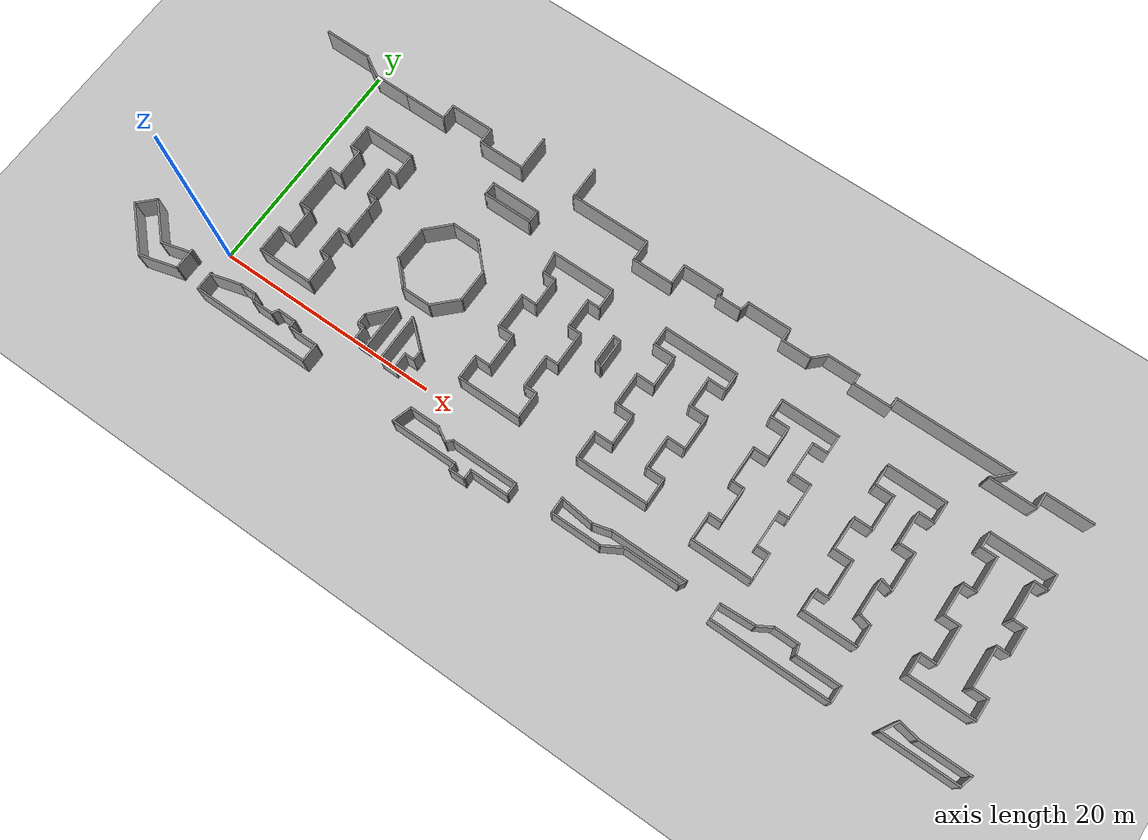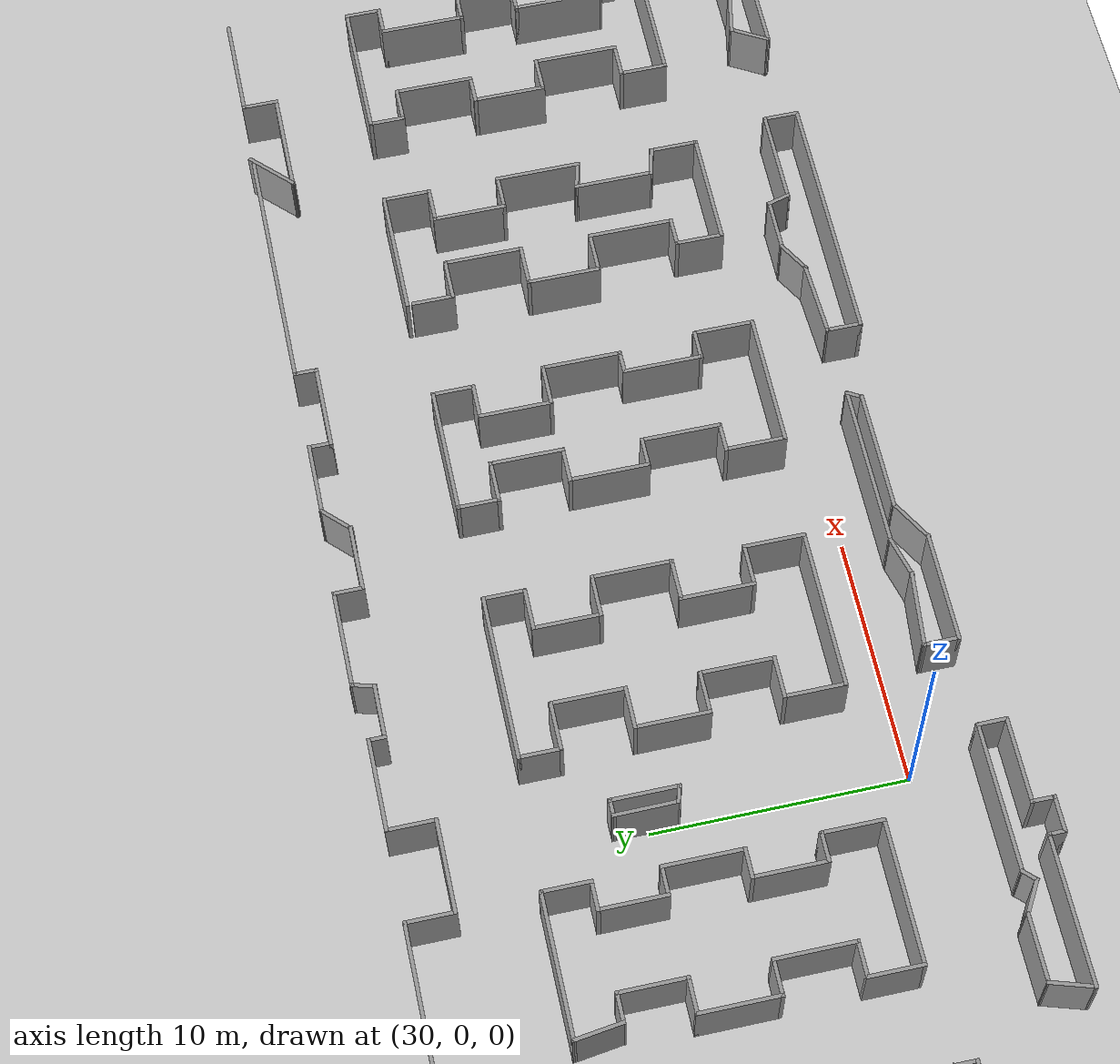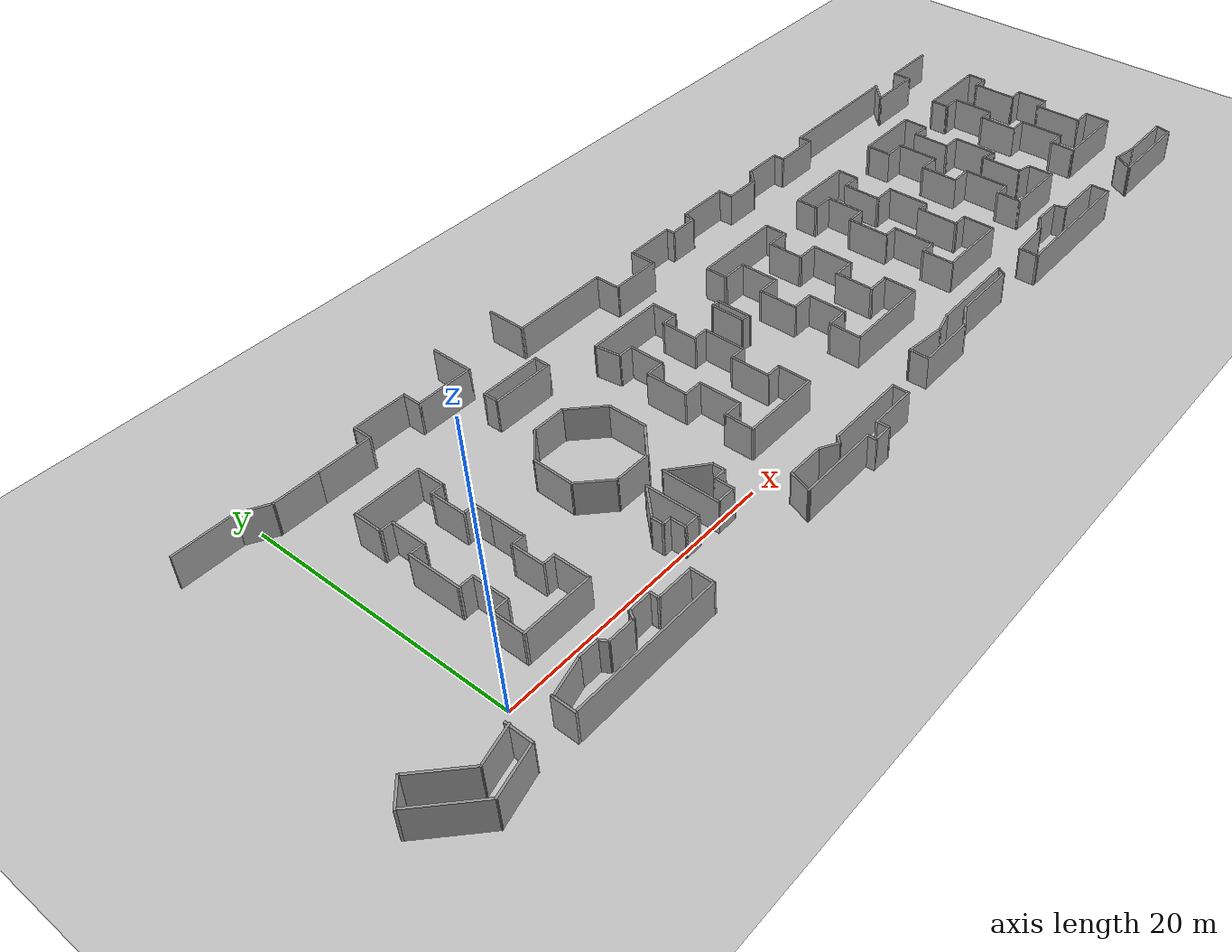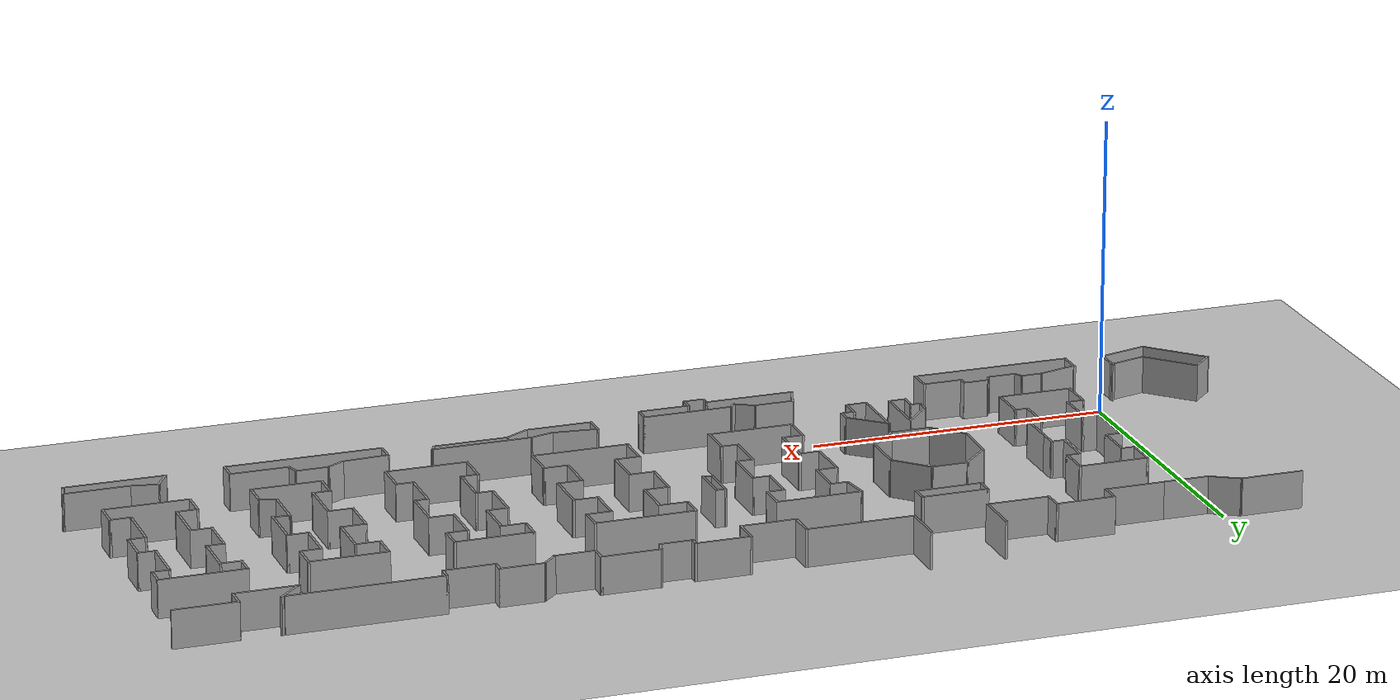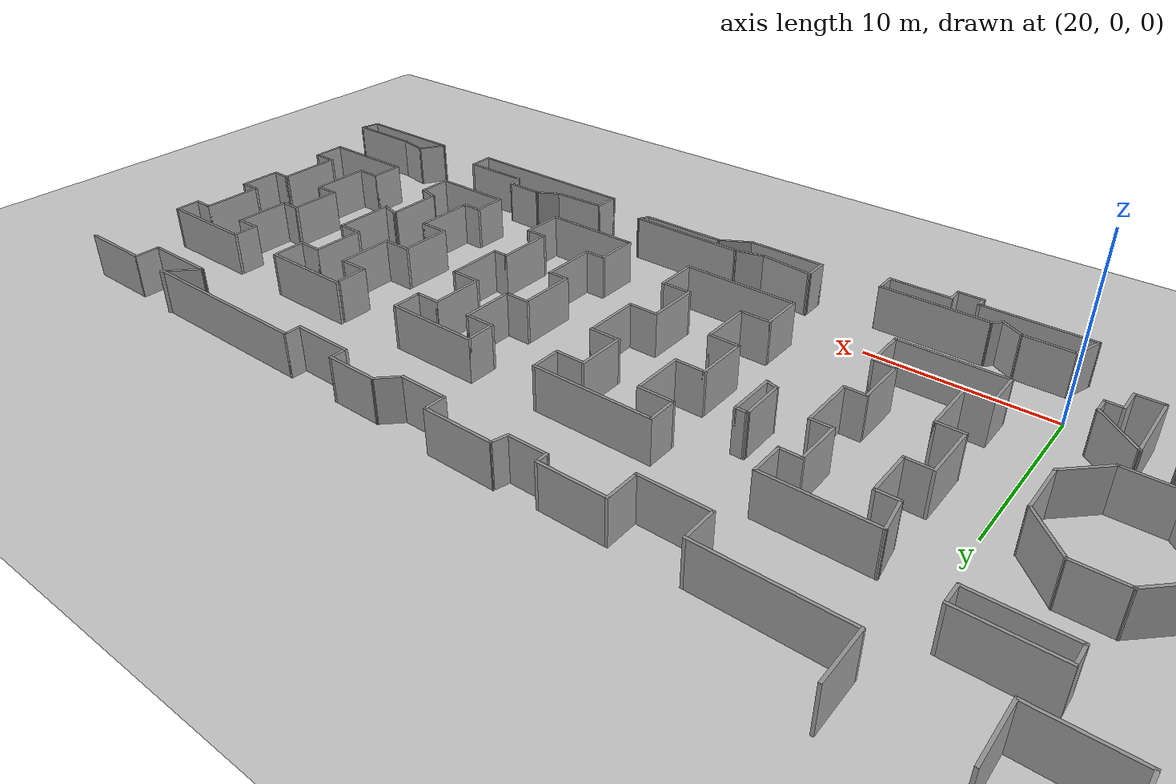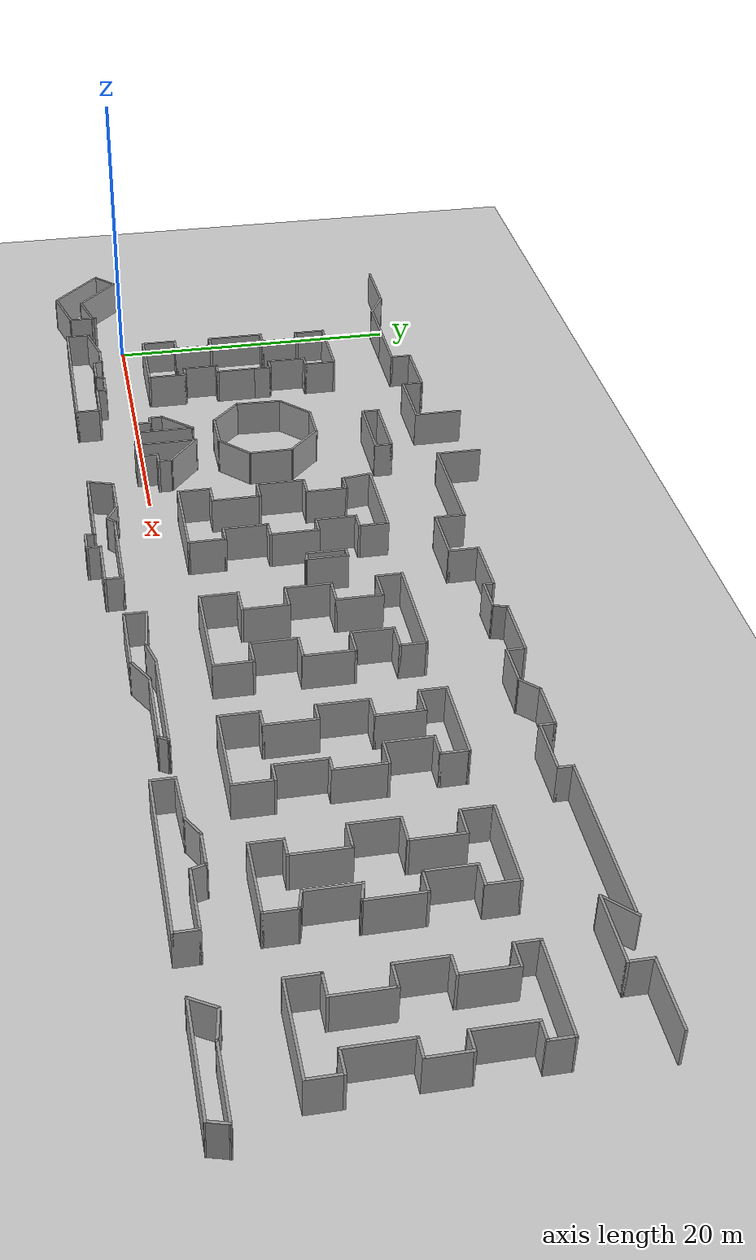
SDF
<sdf version="1.6">
 <world name="default">
  <light name="sun" type="directional">
   <pose>0 0 10 0 -0 0</pose>
   <diffuse>0.8 0.8 0.8 1</diffuse>
   <specular>0.1 0.1 0.1 1</specular>
   <attenuation>
    <range>1000</range>
    <constant>0.9</constant>
    <linear>0.01</linear>
    <quadratic>0.001</quadratic>
   </attenuation>
   <direction>-0.5 0.5 -1</direction>
  </light>
  <model name="ground_plane">
   <static>1</static>
   <link name="link">
    <collision name="collision">
     <geometry><plane><normal>0 0 1</normal><size>100 100</size></plane></geometry>
     <surface><friction><ode><mu>100</mu><mu2>50</mu2></ode></friction></surface>
    </collision>
    <visual name="visual">
     <cast_shadows>0</cast_shadows>
     <geometry><plane><normal>0 0 1</normal><size>100 100</size></plane></geometry>
     <material>
      <script><uri>file://media/materials/scripts/gazebo.material</uri><name>Gazebo/Grey</name></script>
     </material>
    </visual>
   </link>
  </model>
  <gravity>0 0 -9.8</gravity>
  <magnetic_field>6e-06 2.3e-05 -4.2e-05</magnetic_field>
  <atmosphere type="adiabatic"/>
  <physics name="default_physics" default="0" type="ode">
   <max_step_size>0.001</max_step_size>
   <real_time_factor>1</real_time_factor>
   <real_time_update_rate>1000</real_time_update_rate>
  </physics>
  <scene><ambient>0.4 0.4 0.4 1</ambient><background>0.7 0.7 0.7 1</background><shadows>1</shadows></scene>
  <spherical_coordinates>
   <surface_model>EARTH_WGS84</surface_model>
   <latitude_deg>0</latitude_deg>
   <longitude_deg>0</longitude_deg>
   <elevation>0</elevation>
   <heading_deg>0</heading_deg>
  </spherical_coordinates>
  <model name="airport">
   <pose>30.6301 8.89323 0 0 -0 0</pose>
   <link name="Wall_10">
    <collision name="Wall_10_Collision">
     <geometry><box><size>5 0.15 2.5</size></box></geometry>
     <pose>0 0 1.25 0 -0 0</pose>
    </collision>
    <visual name="Wall_10_Visual">
     <pose>0 0 1.25 0 -0 0</pose>
     <geometry><box><size>5 0.15 2.5</size></box></geometry>
     <material>
      <script><uri>file://media/materials/scripts/gazebo.material</uri><name>Gazebo/Grey</name></script>
      <ambient>1 1 1 1</ambient>
     </material>
     <meta><layer>0</layer></meta>
    </visual>
    <pose>-25.3926 -7.51536 0 0 -0 3.14159</pose>
   </link>
   <link name="Wall_100">
    <collision name="Wall_100_Collision">
     <geometry><box><size>2.5 0.15 2.5</size></box></geometry>
     <pose>0 0 1.25 0 -0 0</pose>
    </collision>
    <visual name="Wall_100_Visual">
     <pose>0 0 1.25 0 -0 0</pose>
     <geometry><box><size>2.5 0.15 2.5</size></box></geometry>
     <material>
      <script><uri>file://media/materials/scripts/gazebo.material</uri><name>Gazebo/Grey</name></script>
      <ambient>1 1 1 1</ambient>
     </material>
     <meta><layer>0</layer></meta>
    </visual>
    <pose>-2.79356 -5.95307 0 0 0 -1.5708</pose>
   </link>
   <link name="Wall_101">
    <collision name="Wall_101_Collision">
     <geometry><box><size>5.75 0.15 2.5</size></box></geometry>
     <pose>0 0 1.25 0 -0 0</pose>
    </collision>
    <visual name="Wall_101_Visual">
     <pose>0 0 1.25 0 -0 0</pose>
     <geometry><box><size>5.75 0.15 2.5</size></box></geometry>
     <material>
      <script><uri>file://media/materials/scripts/gazebo.material</uri><name>Gazebo/Grey</name></script>
      <ambient>1 1 1 1</ambient>
     </material>
     <meta><layer>0</layer></meta>
    </visual>
    <pose>-5.59356 -7.12807 0 0 -0 3.14159</pose>
   </link>
   <link name="Wall_102">
    <collision name="Wall_102_Collision">
     <geometry><box><size>2.25 0.15 2.5</size></box></geometry>
     <pose>0 0 1.25 0 -0 0</pose>
    </collision>
    <visual name="Wall_102_Visual">
     <pose>0 0 1.25 0 -0 0</pose>
     <geometry><box><size>2.25 0.15 2.5</size></box></geometry>
     <material>
      <script><uri>file://media/materials/scripts/gazebo.material</uri><name>Gazebo/Grey</name></script>
      <ambient>1 1 1 1</ambient>
     </material>
     <meta><layer>0</layer></meta>
    </visual>
    <pose>-8.39356 -6.07807 0 0 -0 1.5708</pose>
   </link>
   <link name="Wall_103">
    <collision name="Wall_103_Collision">
     <geometry><box><size>1.5 0.15 2.5</size></box></geometry>
     <pose>0 0 1.25 0 -0 0</pose>
    </collision>
    <visual name="Wall_103_Visual">
     <pose>0 0 1.25 0 -0 0</pose>
     <geometry><box><size>1.5 0.15 2.5</size></box></geometry>
     <material>
      <script><uri>file://media/materials/scripts/gazebo.material</uri><name>Gazebo/Grey</name></script>
      <ambient>1 1 1 1</ambient>
     </material>
     <meta><layer>0</layer></meta>
    </visual>
    <pose>-7.71856 -5.02807 0 0 -0 0</pose>
   </link>
   <link name="Wall_104">
    <collision name="Wall_104_Collision">
     <geometry><box><size>3.25 0.15 2.5</size></box></geometry>
     <pose>0 0 1.25 0 -0 0</pose>
    </collision>
    <visual name="Wall_104_Visual">
     <pose>0 0 1.25 0 -0 0</pose>
     <geometry><box><size>3.25 0.15 2.5</size></box></geometry>
     <material>
      <script><uri>file://media/materials/scripts/gazebo.material</uri><name>Gazebo/Grey</name></script>
      <ambient>1 1 1 1</ambient>
     </material>
     <meta><layer>0</layer></meta>
    </visual>
    <pose>-7.04356 -3.47807 0 0 -0 1.5708</pose>
   </link>
   <link name="Wall_105">
    <collision name="Wall_105_Collision">
     <geometry><box><size>1.5 0.15 2.5</size></box></geometry>
     <pose>0 0 1.25 0 -0 0</pose>
    </collision>
    <visual name="Wall_105_Visual">
     <pose>0 0 1.25 0 -0 0</pose>
     <geometry><box><size>1.5 0.15 2.5</size></box></geometry>
     <material>
      <script><uri>file://media/materials/scripts/gazebo.material</uri><name>Gazebo/Grey</name></script>
      <ambient>1 1 1 1</ambient>
     </material>
     <meta><layer>0</layer></meta>
    </visual>
    <pose>-7.71856 -1.92807 0 0 -0 3.14159</pose>
   </link>
   <link name="Wall_106">
    <collision name="Wall_106_Collision">
     <geometry><box><size>3.25 0.15 2.5</size></box></geometry>
     <pose>0 0 1.25 0 -0 0</pose>
    </collision>
    <visual name="Wall_106_Visual">
     <pose>0 0 1.25 0 -0 0</pose>
     <geometry><box><size>3.25 0.15 2.5</size></box></geometry>
     <material>
      <script><uri>file://media/materials/scripts/gazebo.material</uri><name>Gazebo/Grey</name></script>
      <ambient>1 1 1 1</ambient>
     </material>
     <meta><layer>0</layer></meta>
    </visual>
    <pose>-8.39356 -0.378066 0 0 -0 1.5708</pose>
   </link>
   <link name="Wall_107">
    <collision name="Wall_107_Collision">
     <geometry><box><size>1.5 0.15 2.5</size></box></geometry>
     <pose>0 0 1.25 0 -0 0</pose>
    </collision>
    <visual name="Wall_107_Visual">
     <pose>0 0 1.25 0 -0 0</pose>
     <geometry><box><size>1.5 0.15 2.5</size></box></geometry>
     <material>
      <script><uri>file://media/materials/scripts/gazebo.material</uri><name>Gazebo/Grey</name></script>
      <ambient>1 1 1 1</ambient>
     </material>
     <meta><layer>0</layer></meta>
    </visual>
    <pose>-7.71856 1.17193 0 0 -0 0</pose>
   </link>
   <link name="Wall_108">
    <collision name="Wall_108_Collision">
     <geometry><box><size>2.75 0.15 2.5</size></box></geometry>
     <pose>0 0 1.25 0 -0 0</pose>
    </collision>
    <visual name="Wall_108_Visual">
     <pose>0 0 1.25 0 -0 0</pose>
     <geometry><box><size>2.75 0.15 2.5</size></box></geometry>
     <material>
      <script><uri>file://media/materials/scripts/gazebo.material</uri><name>Gazebo/Grey</name></script>
      <ambient>1 1 1 1</ambient>
     </material>
     <meta><layer>0</layer></meta>
    </visual>
    <pose>-7.04356 2.47193 0 0 -0 1.5708</pose>
   </link>
   <link name="Wall_109">
    <collision name="Wall_109_Collision">
     <geometry><box><size>1.25 0.15 2.5</size></box></geometry>
     <pose>0 0 1.25 0 -0 0</pose>
    </collision>
    <visual name="Wall_109_Visual">
     <pose>0 0 1.25 0 -0 0</pose>
     <geometry><box><size>1.25 0.15 2.5</size></box></geometry>
     <material>
      <script><uri>file://media/materials/scripts/gazebo.material</uri><name>Gazebo/Grey</name></script>
      <ambient>1 1 1 1</ambient>
     </material>
     <meta><layer>0</layer></meta>
    </visual>
    <pose>-7.59356 3.77193 0 0 -0 3.14159</pose>
   </link>
   <link name="Wall_11">
    <collision name="Wall_11_Collision">
     <geometry><box><size>2.5 0.15 2.5</size></box></geometry>
     <pose>0 0 1.25 0 -0 0</pose>
    </collision>
    <visual name="Wall_11_Visual">
     <pose>0 0 1.25 0 -0 0</pose>
     <geometry><box><size>2.5 0.15 2.5</size></box></geometry>
     <material>
      <script><uri>file://media/materials/scripts/gazebo.material</uri><name>Gazebo/Grey</name></script>
      <ambient>1 1 1 1</ambient>
     </material>
     <meta><layer>0</layer></meta>
    </visual>
    <pose>-27.8176 -6.34036 0 0 -0 1.5708</pose>
   </link>
   <link name="Wall_110">
    <collision name="Wall_110_Collision">
     <geometry><box><size>2.01681 0.15 2.5</size></box></geometry>
     <pose>0 0 1.25 0 -0 0</pose>
    </collision>
    <visual name="Wall_110_Visual">
     <pose>0 0 1.25 0 -0 0</pose>
     <geometry><box><size>2.01681 0.15 2.5</size></box></geometry>
     <material>
      <script><uri>file://media/materials/scripts/gazebo.material</uri><name>Gazebo/Grey</name></script>
      <ambient>1 1 1 1</ambient>
     </material>
     <meta><layer>0</layer></meta>
    </visual>
    <pose>-8.26856 4.69693 0 0 -0 1.70512</pose>
   </link>
   <link name="Wall_112">
    <collision name="Wall_112_Collision">
     <geometry><box><size>1.25 0.15 2.5</size></box></geometry>
     <pose>0 0 1.25 0 -0 0</pose>
    </collision>
    <visual name="Wall_112_Visual">
     <pose>0 0 1.25 0 -0 0</pose>
     <geometry><box><size>1.25 0.15 2.5</size></box></geometry>
     <material>
      <script><uri>file://media/materials/scripts/gazebo.material</uri><name>Gazebo/Grey</name></script>
      <ambient>1 1 1 1</ambient>
     </material>
     <meta><layer>0</layer></meta>
    </visual>
    <pose>-15.9751 7.24364 0 0 0 -1.5708</pose>
   </link>
   <link name="Wall_113">
    <collision name="Wall_113_Collision">
     <geometry><box><size>4.5 0.15 2.5</size></box></geometry>
     <pose>0 0 1.25 0 -0 0</pose>
    </collision>
    <visual name="Wall_113_Visual">
     <pose>0 0 1.25 0 -0 0</pose>
     <geometry><box><size>4.5 0.15 2.5</size></box></geometry>
     <material>
      <script><uri>file://media/materials/scripts/gazebo.material</uri><name>Gazebo/Grey</name></script>
      <ambient>1 1 1 1</ambient>
     </material>
     <meta><layer>0</layer></meta>
    </visual>
    <pose>-13.8001 6.69364 0 0 -0 0</pose>
   </link>
   <link name="Wall_114">
    <collision name="Wall_114_Collision">
     <geometry><box><size>1.25 0.15 2.5</size></box></geometry>
     <pose>0 0 1.25 0 -0 0</pose>
    </collision>
    <visual name="Wall_114_Visual">
     <pose>0 0 1.25 0 -0 0</pose>
     <geometry><box><size>1.25 0.15 2.5</size></box></geometry>
     <material>
      <script><uri>file://media/materials/scripts/gazebo.material</uri><name>Gazebo/Grey</name></script>
      <ambient>1 1 1 1</ambient>
     </material>
     <meta><layer>0</layer></meta>
    </visual>
    <pose>-11.6251 7.24364 0 0 -0 1.5708</pose>
   </link>
   <link name="Wall_115">
    <collision name="Wall_115_Collision">
     <geometry><box><size>4.5 0.15 2.5</size></box></geometry>
     <pose>0 0 1.25 0 -0 0</pose>
    </collision>
    <visual name="Wall_115_Visual">
     <pose>0 0 1.25 0 -0 0</pose>
     <geometry><box><size>4.5 0.15 2.5</size></box></geometry>
     <material>
      <script><uri>file://media/materials/scripts/gazebo.material</uri><name>Gazebo/Grey</name></script>
      <ambient>1 1 1 1</ambient>
     </material>
     <meta><layer>0</layer></meta>
    </visual>
    <pose>-13.8001 7.79364 0 0 -0 3.14159</pose>
   </link>
   <link name="Wall_117">
    <collision name="Wall_117_Collision">
     <geometry><box><size>4 0.15 2.5</size></box></geometry>
     <pose>0 0 1.25 0 -0 0</pose>
    </collision>
    <visual name="Wall_117_Visual">
     <pose>0 0 1.25 0 -0 0</pose>
     <geometry><box><size>4 0.15 2.5</size></box></geometry>
     <material>
      <script><uri>file://media/materials/scripts/gazebo.material</uri><name>Gazebo/Grey</name></script>
      <ambient>1 1 1 1</ambient>
     </material>
     <meta><layer>0</layer></meta>
    </visual>
    <pose>-15.8825 -7.22328 0 0 0 -1.5708</pose>
   </link>
   <link name="Wall_118">
    <collision name="Wall_118_Collision">
     <geometry><box><size>1.25 0.15 2.5</size></box></geometry>
     <pose>0 0 1.25 0 -0 0</pose>
    </collision>
    <visual name="Wall_118_Visual">
     <pose>0 0 1.25 0 -0 0</pose>
     <geometry><box><size>1.25 0.15 2.5</size></box></geometry>
     <material>
      <script><uri>file://media/materials/scripts/gazebo.material</uri><name>Gazebo/Grey</name></script>
      <ambient>1 1 1 1</ambient>
     </material>
     <meta><layer>0</layer></meta>
    </visual>
    <pose>-16.4325 -9.14828 0 0 -0 3.14159</pose>
   </link>
   <link name="Wall_119">
    <collision name="Wall_119_Collision">
     <geometry><box><size>1.25 0.15 2.5</size></box></geometry>
     <pose>0 0 1.25 0 -0 0</pose>
    </collision>
    <visual name="Wall_119_Visual">
     <pose>0 0 1.25 0 -0 0</pose>
     <geometry><box><size>1.25 0.15 2.5</size></box></geometry>
     <material>
      <script><uri>file://media/materials/scripts/gazebo.material</uri><name>Gazebo/Grey</name></script>
      <ambient>1 1 1 1</ambient>
     </material>
     <meta><layer>0</layer></meta>
    </visual>
    <pose>-16.9825 -8.59828 0 0 -0 1.5708</pose>
   </link>
   <link name="Wall_12">
    <collision name="Wall_12_Collision">
     <geometry><box><size>1.25 0.15 2.5</size></box></geometry>
     <pose>0 0 1.25 0 -0 0</pose>
    </collision>
    <visual name="Wall_12_Visual">
     <pose>0 0 1.25 0 -0 0</pose>
     <geometry><box><size>1.25 0.15 2.5</size></box></geometry>
     <material>
      <script><uri>file://media/materials/scripts/gazebo.material</uri><name>Gazebo/Grey</name></script>
      <ambient>1 1 1 1</ambient>
     </material>
     <meta><layer>0</layer></meta>
    </visual>
    <pose>-27.2676 -5.16536 0 0 -0 0</pose>
   </link>
   <link name="Wall_120">
    <collision name="Wall_120_Collision">
     <geometry><box><size>0.75 0.15 2.5</size></box></geometry>
     <pose>0 0 1.25 0 -0 0</pose>
    </collision>
    <visual name="Wall_120_Visual">
     <pose>0 0 1.25 0 -0 0</pose>
     <geometry><box><size>0.75 0.15 2.5</size></box></geometry>
     <material>
      <script><uri>file://media/materials/scripts/gazebo.material</uri><name>Gazebo/Grey</name></script>
      <ambient>1 1 1 1</ambient>
     </material>
     <meta><layer>0</layer></meta>
    </visual>
    <pose>-17.2825 -8.04828 0 0 -0 3.14159</pose>
   </link>
   <link name="Wall_121">
    <collision name="Wall_121_Collision">
     <geometry><box><size>1 0.15 2.5</size></box></geometry>
     <pose>0 0 1.25 0 -0 0</pose>
    </collision>
    <visual name="Wall_121_Visual">
     <pose>0 0 1.25 0 -0 0</pose>
     <geometry><box><size>1 0.15 2.5</size></box></geometry>
     <material>
      <script><uri>file://media/materials/scripts/gazebo.material</uri><name>Gazebo/Grey</name></script>
      <ambient>1 1 1 1</ambient>
     </material>
     <meta><layer>0</layer></meta>
    </visual>
    <pose>-17.5825 -7.62328 0 0 -0 1.5708</pose>
   </link>
   <link name="Wall_122">
    <collision name="Wall_122_Collision">
     <geometry><box><size>2.69951 0.15 2.5</size></box></geometry>
     <pose>0 0 1.25 0 -0 0</pose>
    </collision>
    <visual name="Wall_122_Visual">
     <pose>0 0 1.25 0 -0 0</pose>
     <geometry><box><size>2.69951 0.15 2.5</size></box></geometry>
     <material>
      <script><uri>file://media/materials/scripts/gazebo.material</uri><name>Gazebo/Grey</name></script>
      <ambient>1 1 1 1</ambient>
     </material>
     <meta><layer>0</layer></meta>
    </visual>
    <pose>-16.7325 -6.24828 0 0 -0 0.840897</pose>
   </link>
   <link name="Wall_124">
    <collision name="Wall_124_Collision">
     <geometry><box><size>4.25 0.15 2.5</size></box></geometry>
     <pose>0 0 1.25 0 -0 0</pose>
    </collision>
    <visual name="Wall_124_Visual">
     <pose>0 0 1.25 0 -0 0</pose>
     <geometry><box><size>4.25 0.15 2.5</size></box></geometry>
     <material>
      <script><uri>file://media/materials/scripts/gazebo.material</uri><name>Gazebo/Grey</name></script>
      <ambient>1 1 1 1</ambient>
     </material>
     <meta><layer>0</layer></meta>
    </visual>
    <pose>-14.3559 -7.30202 0 0 0 -1.5708</pose>
   </link>
   <link name="Wall_125">
    <collision name="Wall_125_Collision">
     <geometry><box><size>1.5 0.15 2.5</size></box></geometry>
     <pose>0 0 1.25 0 -0 0</pose>
    </collision>
    <visual name="Wall_125_Visual">
     <pose>0 0 1.25 0 -0 0</pose>
     <geometry><box><size>1.5 0.15 2.5</size></box></geometry>
     <material>
      <script><uri>file://media/materials/scripts/gazebo.material</uri><name>Gazebo/Grey</name></script>
      <ambient>1 1 1 1</ambient>
     </material>
     <meta><layer>0</layer></meta>
    </visual>
    <pose>-13.6809 -9.35202 0 0 -0 0</pose>
   </link>
   <link name="Wall_126">
    <collision name="Wall_126_Collision">
     <geometry><box><size>1.5 0.15 2.5</size></box></geometry>
     <pose>0 0 1.25 0 -0 0</pose>
    </collision>
    <visual name="Wall_126_Visual">
     <pose>0 0 1.25 0 -0 0</pose>
     <geometry><box><size>1.5 0.15 2.5</size></box></geometry>
     <material>
      <script><uri>file://media/materials/scripts/gazebo.material</uri><name>Gazebo/Grey</name></script>
      <ambient>1 1 1 1</ambient>
     </material>
     <meta><layer>0</layer></meta>
    </visual>
    <pose>-13.0059 -8.67702 0 0 -0 1.5708</pose>
   </link>
   <link name="Wall_127">
    <collision name="Wall_127_Collision">
     <geometry><box><size>1 0.15 2.5</size></box></geometry>
     <pose>0 0 1.25 0 -0 0</pose>
    </collision>
    <visual name="Wall_127_Visual">
     <pose>0 0 1.25 0 -0 0</pose>
     <geometry><box><size>1 0.15 2.5</size></box></geometry>
     <material>
      <script><uri>file://media/materials/scripts/gazebo.material</uri><name>Gazebo/Grey</name></script>
      <ambient>1 1 1 1</ambient>
     </material>
     <meta><layer>0</layer></meta>
    </visual>
    <pose>-12.5809 -8.00202 0 0 -0 0</pose>
   </link>
   <link name="Wall_128">
    <collision name="Wall_128_Collision">
     <geometry><box><size>1 0.15 2.5</size></box></geometry>
     <pose>0 0 1.25 0 -0 0</pose>
    </collision>
    <visual name="Wall_128_Visual">
     <pose>0 0 1.25 0 -0 0</pose>
     <geometry><box><size>1 0.15 2.5</size></box></geometry>
     <material>
      <script><uri>file://media/materials/scripts/gazebo.material</uri><name>Gazebo/Grey</name></script>
      <ambient>1 1 1 1</ambient>
     </material>
     <meta><layer>0</layer></meta>
    </visual>
    <pose>-12.1559 -7.57702 0 0 -0 1.5708</pose>
   </link>
   <link name="Wall_129">
    <collision name="Wall_129_Collision">
     <geometry><box><size>3.05689 0.15 2.5</size></box></geometry>
     <pose>0 0 1.25 0 -0 0</pose>
    </collision>
    <visual name="Wall_129_Visual">
     <pose>0 0 1.25 0 -0 0</pose>
     <geometry><box><size>3.05689 0.15 2.5</size></box></geometry>
     <material>
      <script><uri>file://media/materials/scripts/gazebo.material</uri><name>Gazebo/Grey</name></script>
      <ambient>1 1 1 1</ambient>
     </material>
     <meta><layer>0</layer></meta>
    </visual>
    <pose>-13.2559 -6.20202 0 0 -0 2.42923</pose>
   </link>
   <link name="Wall_13">
    <collision name="Wall_13_Collision">
     <geometry><box><size>2.75 0.15 2.5</size></box></geometry>
     <pose>0 0 1.25 0 -0 0</pose>
    </collision>
    <visual name="Wall_13_Visual">
     <pose>0 0 1.25 0 -0 0</pose>
     <geometry><box><size>2.75 0.15 2.5</size></box></geometry>
     <material>
      <script><uri>file://media/materials/scripts/gazebo.material</uri><name>Gazebo/Grey</name></script>
      <ambient>1 1 1 1</ambient>
     </material>
     <meta><layer>0</layer></meta>
    </visual>
    <pose>-26.7176 -3.86536 0 0 -0 1.5708</pose>
   </link>
   <link name="Wall_131">
    <collision name="Wall_131_Collision">
     <geometry><box><size>2.75 0.15 2.5</size></box></geometry>
     <pose>0 0 1.25 0 -0 0</pose>
    </collision>
    <visual name="Wall_131_Visual">
     <pose>0 0 1.25 0 -0 0</pose>
     <geometry><box><size>2.75 0.15 2.5</size></box></geometry>
     <material>
      <script><uri>file://media/materials/scripts/gazebo.material</uri><name>Gazebo/Grey</name></script>
      <ambient>1 1 1 1</ambient>
     </material>
     <meta><layer>0</layer></meta>
    </visual>
    <pose>-8.67435 -11.2295 0 0 -0 0</pose>
   </link>
   <link name="Wall_132">
    <collision name="Wall_132_Collision">
     <geometry><box><size>1.5 0.15 2.5</size></box></geometry>
     <pose>0 0 1.25 0 -0 0</pose>
    </collision>
    <visual name="Wall_132_Visual">
     <pose>0 0 1.25 0 -0 0</pose>
     <geometry><box><size>1.5 0.15 2.5</size></box></geometry>
     <material>
      <script><uri>file://media/materials/scripts/gazebo.material</uri><name>Gazebo/Grey</name></script>
      <ambient>1 1 1 1</ambient>
     </material>
     <meta><layer>0</layer></meta>
    </visual>
    <pose>-6.78978 -11.567 0 0 0 -0.523599</pose>
   </link>
   <link name="Wall_133">
    <collision name="Wall_133_Collision">
     <geometry><box><size>0.75 0.15 2.5</size></box></geometry>
     <pose>0 0 1.25 0 -0 0</pose>
    </collision>
    <visual name="Wall_133_Visual">
     <pose>0 0 1.25 0 -0 0</pose>
     <geometry><box><size>0.75 0.15 2.5</size></box></geometry>
     <material>
      <script><uri>file://media/materials/scripts/gazebo.material</uri><name>Gazebo/Grey</name></script>
      <ambient>1 1 1 1</ambient>
     </material>
     <meta><layer>0</layer></meta>
    </visual>
    <pose>-5.99308 -11.6924 0 0 -0 0.785398</pose>
   </link>
   <link name="Wall_134">
    <collision name="Wall_134_Collision">
     <geometry><box><size>6 0.15 2.5</size></box></geometry>
     <pose>0 0 1.25 0 -0 0</pose>
    </collision>
    <visual name="Wall_134_Visual">
     <pose>0 0 1.25 0 -0 0</pose>
     <geometry><box><size>6 0.15 2.5</size></box></geometry>
     <material>
      <script><uri>file://media/materials/scripts/gazebo.material</uri><name>Gazebo/Grey</name></script>
      <ambient>1 1 1 1</ambient>
     </material>
     <meta><layer>0</layer></meta>
    </visual>
    <pose>-2.85595 -11.4803 0 0 -0 0</pose>
   </link>
   <link name="Wall_135">
    <collision name="Wall_135_Collision">
     <geometry><box><size>1.25 0.15 2.5</size></box></geometry>
     <pose>0 0 1.25 0 -0 0</pose>
    </collision>
    <visual name="Wall_135_Visual">
     <pose>0 0 1.25 0 -0 0</pose>
     <geometry><box><size>1.25 0.15 2.5</size></box></geometry>
     <material>
      <script><uri>file://media/materials/scripts/gazebo.material</uri><name>Gazebo/Grey</name></script>
      <ambient>1 1 1 1</ambient>
     </material>
     <meta><layer>0</layer></meta>
    </visual>
    <pose>0.069051 -12.0303 0 0 0 -1.5708</pose>
   </link>
   <link name="Wall_136">
    <collision name="Wall_136_Collision">
     <geometry><box><size>3.5 0.15 2.5</size></box></geometry>
     <pose>0 0 1.25 0 -0 0</pose>
    </collision>
    <visual name="Wall_136_Visual">
     <pose>0 0 1.25 0 -0 0</pose>
     <geometry><box><size>3.5 0.15 2.5</size></box></geometry>
     <material>
      <script><uri>file://media/materials/scripts/gazebo.material</uri><name>Gazebo/Grey</name></script>
      <ambient>1 1 1 1</ambient>
     </material>
     <meta><layer>0</layer></meta>
    </visual>
    <pose>-1.60595 -12.5803 0 0 -0 3.14159</pose>
   </link>
   <link name="Wall_137">
    <collision name="Wall_137_Collision">
     <geometry><box><size>1 0.15 2.5</size></box></geometry>
     <pose>0 0 1.25 0 -0 0</pose>
    </collision>
    <visual name="Wall_137_Visual">
     <pose>0 0 1.25 0 -0 0</pose>
     <geometry><box><size>1 0.15 2.5</size></box></geometry>
     <material>
      <script><uri>file://media/materials/scripts/gazebo.material</uri><name>Gazebo/Grey</name></script>
      <ambient>1 1 1 1</ambient>
     </material>
     <meta><layer>0</layer></meta>
    </visual>
    <pose>-3.28095 -13.0053 0 0 0 -1.5708</pose>
   </link>
   <link name="Wall_138">
    <collision name="Wall_138_Collision">
     <geometry><box><size>1.5 0.15 2.5</size></box></geometry>
     <pose>0 0 1.25 0 -0 0</pose>
    </collision>
    <visual name="Wall_138_Visual">
     <pose>0 0 1.25 0 -0 0</pose>
     <geometry><box><size>1.5 0.15 2.5</size></box></geometry>
     <material>
      <script><uri>file://media/materials/scripts/gazebo.material</uri><name>Gazebo/Grey</name></script>
      <ambient>1 1 1 1</ambient>
     </material>
     <meta><layer>0</layer></meta>
    </visual>
    <pose>-3.95595 -13.4303 0 0 -0 3.14159</pose>
   </link>
   <link name="Wall_139">
    <collision name="Wall_139_Collision">
     <geometry><box><size>0.75 0.15 2.5</size></box></geometry>
     <pose>0 0 1.25 0 -0 0</pose>
    </collision>
    <visual name="Wall_139_Visual">
     <pose>0 0 1.25 0 -0 0</pose>
     <geometry><box><size>0.75 0.15 2.5</size></box></geometry>
     <material>
      <script><uri>file://media/materials/scripts/gazebo.material</uri><name>Gazebo/Grey</name></script>
      <ambient>1 1 1 1</ambient>
     </material>
     <meta><layer>0</layer></meta>
    </visual>
    <pose>-4.63095 -13.1303 0 0 -0 1.5708</pose>
   </link>
   <link name="Wall_140">
    <collision name="Wall_140_Collision">
     <geometry><box><size>6 0.15 2.5</size></box></geometry>
     <pose>0 0 1.25 0 -0 0</pose>
    </collision>
    <visual name="Wall_140_Visual">
     <pose>0 0 1.25 0 -0 0</pose>
     <geometry><box><size>6 0.15 2.5</size></box></geometry>
     <material>
      <script><uri>file://media/materials/scripts/gazebo.material</uri><name>Gazebo/Grey</name></script>
      <ambient>1 1 1 1</ambient>
     </material>
     <meta><layer>0</layer></meta>
    </visual>
    <pose>-7.55595 -12.8303 0 0 -0 3.14159</pose>
   </link>
   <link name="Wall_141">
    <collision name="Wall_141_Collision">
     <geometry><box><size>1.82899 0.15 2.5</size></box></geometry>
     <pose>0 0 1.25 0 -0 0</pose>
    </collision>
    <visual name="Wall_141_Visual">
     <pose>0 0 1.25 0 -0 0</pose>
     <geometry><box><size>1.82899 0.15 2.5</size></box></geometry>
     <material>
      <script><uri>file://media/materials/scripts/gazebo.material</uri><name>Gazebo/Grey</name></script>
      <ambient>1 1 1 1</ambient>
     </material>
     <meta><layer>0</layer></meta>
    </visual>
    <pose>-10.2276 -12.0299 0 0 -0 1.26429</pose>
   </link>
   <link name="Wall_146">
    <collision name="Wall_146_Collision">
     <geometry><box><size>2 0.15 2.5</size></box></geometry>
     <pose>0 0 1.25 0 -0 0</pose>
    </collision>
    <visual name="Wall_146_Visual">
     <pose>0 0 1.25 0 -0 0</pose>
     <geometry><box><size>2 0.15 2.5</size></box></geometry>
     <material>
      <script><uri>file://media/materials/scripts/gazebo.material</uri><name>Gazebo/Grey</name></script>
      <ambient>1 1 1 1</ambient>
     </material>
     <meta><layer>0</layer></meta>
    </visual>
    <pose>3.39066 3.77039 0 0 -0 0</pose>
   </link>
   <link name="Wall_150">
    <collision name="Wall_150_Collision">
     <geometry><box><size>3 0.15 2.5</size></box></geometry>
     <pose>0 0 1.25 0 -0 0</pose>
    </collision>
    <visual name="Wall_150_Visual">
     <pose>0 0 1.25 0 -0 0</pose>
     <geometry><box><size>3 0.15 2.5</size></box></geometry>
     <material>
      <script><uri>file://media/materials/scripts/gazebo.material</uri><name>Gazebo/Grey</name></script>
      <ambient>1 1 1 1</ambient>
     </material>
     <meta><layer>0</layer></meta>
    </visual>
    <pose>4.31566 2.34539 0 0 0 -1.5708</pose>
   </link>
   <link name="Wall_151">
    <collision name="Wall_151_Collision">
     <geometry><box><size>1.75 0.15 2.5</size></box></geometry>
     <pose>0 0 1.25 0 -0 0</pose>
    </collision>
    <visual name="Wall_151_Visual">
     <pose>0 0 1.25 0 -0 0</pose>
     <geometry><box><size>1.75 0.15 2.5</size></box></geometry>
     <material>
      <script><uri>file://media/materials/scripts/gazebo.material</uri><name>Gazebo/Grey</name></script>
      <ambient>1 1 1 1</ambient>
     </material>
     <meta><layer>0</layer></meta>
    </visual>
    <pose>3.51566 0.920386 0 0 -0 3.14159</pose>
   </link>
   <link name="Wall_152">
    <collision name="Wall_152_Collision">
     <geometry><box><size>3 0.15 2.5</size></box></geometry>
     <pose>0 0 1.25 0 -0 0</pose>
    </collision>
    <visual name="Wall_152_Visual">
     <pose>0 0 1.25 0 -0 0</pose>
     <geometry><box><size>3 0.15 2.5</size></box></geometry>
     <material>
      <script><uri>file://media/materials/scripts/gazebo.material</uri><name>Gazebo/Grey</name></script>
      <ambient>1 1 1 1</ambient>
     </material>
     <meta><layer>0</layer></meta>
    </visual>
    <pose>2.71566 -0.504614 0 0 0 -1.5708</pose>
   </link>
   <link name="Wall_153">
    <collision name="Wall_153_Collision">
     <geometry><box><size>1.75 0.15 2.5</size></box></geometry>
     <pose>0 0 1.25 0 -0 0</pose>
    </collision>
    <visual name="Wall_153_Visual">
     <pose>0 0 1.25 0 -0 0</pose>
     <geometry><box><size>1.75 0.15 2.5</size></box></geometry>
     <material>
      <script><uri>file://media/materials/scripts/gazebo.material</uri><name>Gazebo/Grey</name></script>
      <ambient>1 1 1 1</ambient>
     </material>
     <meta><layer>0</layer></meta>
    </visual>
    <pose>3.51566 -1.92961 0 0 -0 0</pose>
   </link>
   <link name="Wall_154">
    <collision name="Wall_154_Collision">
     <geometry><box><size>3 0.15 2.5</size></box></geometry>
     <pose>0 0 1.25 0 -0 0</pose>
    </collision>
    <visual name="Wall_154_Visual">
     <pose>0 0 1.25 0 -0 0</pose>
     <geometry><box><size>3 0.15 2.5</size></box></geometry>
     <material>
      <script><uri>file://media/materials/scripts/gazebo.material</uri><name>Gazebo/Grey</name></script>
      <ambient>1 1 1 1</ambient>
     </material>
     <meta><layer>0</layer></meta>
    </visual>
    <pose>4.31566 -3.35461 0 0 0 -1.5708</pose>
   </link>
   <link name="Wall_155">
    <collision name="Wall_155_Collision">
     <geometry><box><size>1.75 0.15 2.5</size></box></geometry>
     <pose>0 0 1.25 0 -0 0</pose>
    </collision>
    <visual name="Wall_155_Visual">
     <pose>0 0 1.25 0 -0 0</pose>
     <geometry><box><size>1.75 0.15 2.5</size></box></geometry>
     <material>
      <script><uri>file://media/materials/scripts/gazebo.material</uri><name>Gazebo/Grey</name></script>
      <ambient>1 1 1 1</ambient>
     </material>
     <meta><layer>0</layer></meta>
    </visual>
    <pose>3.51566 -4.77961 0 0 -0 3.14159</pose>
   </link>
   <link name="Wall_158">
    <collision name="Wall_158_Collision">
     <geometry><box><size>2.5 0.15 2.5</size></box></geometry>
     <pose>0 0 1.25 0 -0 0</pose>
    </collision>
    <visual name="Wall_158_Visual">
     <pose>0 0 1.25 0 -0 0</pose>
     <geometry><box><size>2.5 0.15 2.5</size></box></geometry>
     <material>
      <script><uri>file://media/materials/scripts/gazebo.material</uri><name>Gazebo/Grey</name></script>
      <ambient>1 1 1 1</ambient>
     </material>
     <meta><layer>0</layer></meta>
    </visual>
    <pose>2.71566 -5.95461 0 0 0 -1.5708</pose>
   </link>
   <link name="Wall_159">
    <collision name="Wall_159_Collision">
     <geometry><box><size>6.5 0.15 2.5</size></box></geometry>
     <pose>0 0 1.25 0 -0 0</pose>
    </collision>
    <visual name="Wall_159_Visual">
     <pose>0 0 1.25 0 -0 0</pose>
     <geometry><box><size>6.5 0.15 2.5</size></box></geometry>
     <material>
      <script><uri>file://media/materials/scripts/gazebo.material</uri><name>Gazebo/Grey</name></script>
      <ambient>1 1 1 1</ambient>
     </material>
     <meta><layer>0</layer></meta>
    </visual>
    <pose>5.89066 -7.12961 0 0 -0 0</pose>
   </link>
   <link name="Wall_16">
    <collision name="Wall_16_Collision">
     <geometry><box><size>1.18061 0.15 2.5</size></box></geometry>
     <pose>0 0 1.25 0 -0 0</pose>
    </collision>
    <visual name="Wall_16_Visual">
     <pose>0 0 1.25 0 -0 0</pose>
     <geometry><box><size>1.18061 0.15 2.5</size></box></geometry>
     <material>
      <script><uri>file://media/materials/scripts/gazebo.material</uri><name>Gazebo/Grey</name></script>
      <ambient>1 1 1 1</ambient>
     </material>
     <meta><layer>0</layer></meta>
    </visual>
    <pose>-27.2329 -2.56536 0 0 -0 3.14159</pose>
   </link>
   <link name="Wall_160">
    <collision name="Wall_160_Collision">
     <geometry><box><size>2.5 0.15 2.5</size></box></geometry>
     <pose>0 0 1.25 0 -0 0</pose>
    </collision>
    <visual name="Wall_160_Visual">
     <pose>0 0 1.25 0 -0 0</pose>
     <geometry><box><size>2.5 0.15 2.5</size></box></geometry>
     <material>
      <script><uri>file://media/materials/scripts/gazebo.material</uri><name>Gazebo/Grey</name></script>
      <ambient>1 1 1 1</ambient>
     </material>
     <meta><layer>0</layer></meta>
    </visual>
    <pose>9.06566 -5.95461 0 0 -0 1.5708</pose>
   </link>
   <link name="Wall_161">
    <collision name="Wall_161_Collision">
     <geometry><box><size>1.75 0.15 2.5</size></box></geometry>
     <pose>0 0 1.25 0 -0 0</pose>
    </collision>
    <visual name="Wall_161_Visual">
     <pose>0 0 1.25 0 -0 0</pose>
     <geometry><box><size>1.75 0.15 2.5</size></box></geometry>
     <material>
      <script><uri>file://media/materials/scripts/gazebo.material</uri><name>Gazebo/Grey</name></script>
      <ambient>1 1 1 1</ambient>
     </material>
     <meta><layer>0</layer></meta>
    </visual>
    <pose>8.26566 -4.77961 0 0 -0 3.14159</pose>
   </link>
   <link name="Wall_162">
    <collision name="Wall_162_Collision">
     <geometry><box><size>3 0.15 2.5</size></box></geometry>
     <pose>0 0 1.25 0 -0 0</pose>
    </collision>
    <visual name="Wall_162_Visual">
     <pose>0 0 1.25 0 -0 0</pose>
     <geometry><box><size>3 0.15 2.5</size></box></geometry>
     <material>
      <script><uri>file://media/materials/scripts/gazebo.material</uri><name>Gazebo/Grey</name></script>
      <ambient>1 1 1 1</ambient>
     </material>
     <meta><layer>0</layer></meta>
    </visual>
    <pose>7.46566 -3.35461 0 0 -0 1.5708</pose>
   </link>
   <link name="Wall_163">
    <collision name="Wall_163_Collision">
     <geometry><box><size>1.75 0.15 2.5</size></box></geometry>
     <pose>0 0 1.25 0 -0 0</pose>
    </collision>
    <visual name="Wall_163_Visual">
     <pose>0 0 1.25 0 -0 0</pose>
     <geometry><box><size>1.75 0.15 2.5</size></box></geometry>
     <material>
      <script><uri>file://media/materials/scripts/gazebo.material</uri><name>Gazebo/Grey</name></script>
      <ambient>1 1 1 1</ambient>
     </material>
     <meta><layer>0</layer></meta>
    </visual>
    <pose>8.26566 -1.92961 0 0 -0 0</pose>
   </link>
   <link name="Wall_164">
    <collision name="Wall_164_Collision">
     <geometry><box><size>3.25 0.15 2.5</size></box></geometry>
     <pose>0 0 1.25 0 -0 0</pose>
    </collision>
    <visual name="Wall_164_Visual">
     <pose>0 0 1.25 0 -0 0</pose>
     <geometry><box><size>3.25 0.15 2.5</size></box></geometry>
     <material>
      <script><uri>file://media/materials/scripts/gazebo.material</uri><name>Gazebo/Grey</name></script>
      <ambient>1 1 1 1</ambient>
     </material>
     <meta><layer>0</layer></meta>
    </visual>
    <pose>9.06566 -0.379614 0 0 -0 1.5708</pose>
   </link>
   <link name="Wall_165">
    <collision name="Wall_165_Collision">
     <geometry><box><size>1.75 0.15 2.5</size></box></geometry>
     <pose>0 0 1.25 0 -0 0</pose>
    </collision>
    <visual name="Wall_165_Visual">
     <pose>0 0 1.25 0 -0 0</pose>
     <geometry><box><size>1.75 0.15 2.5</size></box></geometry>
     <material>
      <script><uri>file://media/materials/scripts/gazebo.material</uri><name>Gazebo/Grey</name></script>
      <ambient>1 1 1 1</ambient>
     </material>
     <meta><layer>0</layer></meta>
    </visual>
    <pose>8.26566 1.17039 0 0 -0 3.14159</pose>
   </link>
   <link name="Wall_166">
    <collision name="Wall_166_Collision">
     <geometry><box><size>2.75 0.15 2.5</size></box></geometry>
     <pose>0 0 1.25 0 -0 0</pose>
    </collision>
    <visual name="Wall_166_Visual">
     <pose>0 0 1.25 0 -0 0</pose>
     <geometry><box><size>2.75 0.15 2.5</size></box></geometry>
     <material>
      <script><uri>file://media/materials/scripts/gazebo.material</uri><name>Gazebo/Grey</name></script>
      <ambient>1 1 1 1</ambient>
     </material>
     <meta><layer>0</layer></meta>
    </visual>
    <pose>7.46566 2.47039 0 0 -0 1.5708</pose>
   </link>
   <link name="Wall_167">
    <collision name="Wall_167_Collision">
     <geometry><box><size>1.75 0.15 2.5</size></box></geometry>
     <pose>0 0 1.25 0 -0 0</pose>
    </collision>
    <visual name="Wall_167_Visual">
     <pose>0 0 1.25 0 -0 0</pose>
     <geometry><box><size>1.75 0.15 2.5</size></box></geometry>
     <material>
      <script><uri>file://media/materials/scripts/gazebo.material</uri><name>Gazebo/Grey</name></script>
      <ambient>1 1 1 1</ambient>
     </material>
     <meta><layer>0</layer></meta>
    </visual>
    <pose>8.26566 3.77039 0 0 -0 0</pose>
   </link>
   <link name="Wall_168">
    <collision name="Wall_168_Collision">
     <geometry><box><size>1.75 0.15 2.5</size></box></geometry>
     <pose>0 0 1.25 0 -0 0</pose>
    </collision>
    <visual name="Wall_168_Visual">
     <pose>0 0 1.25 0 -0 0</pose>
     <geometry><box><size>1.75 0.15 2.5</size></box></geometry>
     <material>
      <script><uri>file://media/materials/scripts/gazebo.material</uri><name>Gazebo/Grey</name></script>
      <ambient>1 1 1 1</ambient>
     </material>
     <meta><layer>0</layer></meta>
    </visual>
    <pose>9.06566 4.57039 0 0 -0 1.5708</pose>
   </link>
   <link name="Wall_169">
    <collision name="Wall_169_Collision">
     <geometry><box><size>6.75 0.15 2.5</size></box></geometry>
     <pose>0 0 1.25 0 -0 0</pose>
    </collision>
    <visual name="Wall_169_Visual">
     <pose>0 0 1.25 0 -0 0</pose>
     <geometry><box><size>6.75 0.15 2.5</size></box></geometry>
     <material>
      <script><uri>file://media/materials/scripts/gazebo.material</uri><name>Gazebo/Grey</name></script>
      <ambient>1 1 1 1</ambient>
     </material>
     <meta><layer>0</layer></meta>
    </visual>
    <pose>5.76566 5.37039 0 0 -0 3.14159</pose>
   </link>
   <link name="Wall_17">
    <collision name="Wall_17_Collision">
     <geometry><box><size>4 0.15 2.5</size></box></geometry>
     <pose>0 0 1.25 0 -0 0</pose>
    </collision>
    <visual name="Wall_17_Visual">
     <pose>0 0 1.25 0 -0 0</pose>
     <geometry><box><size>4 0.15 2.5</size></box></geometry>
     <material>
      <script><uri>file://media/materials/scripts/gazebo.material</uri><name>Gazebo/Grey</name></script>
      <ambient>1 1 1 1</ambient>
     </material>
     <meta><layer>0</layer></meta>
    </visual>
    <pose>-27.7482 -0.663492 0 0 -0 1.5708</pose>
   </link>
   <link name="Wall_171">
    <collision name="Wall_171_Collision">
     <geometry><box><size>1.75 0.15 2.5</size></box></geometry>
     <pose>0 0 1.25 0 -0 0</pose>
    </collision>
    <visual name="Wall_171_Visual">
     <pose>0 0 1.25 0 -0 0</pose>
     <geometry><box><size>1.75 0.15 2.5</size></box></geometry>
     <material>
      <script><uri>file://media/materials/scripts/gazebo.material</uri><name>Gazebo/Grey</name></script>
      <ambient>1 1 1 1</ambient>
     </material>
     <meta><layer>0</layer></meta>
    </visual>
    <pose>2.46566 4.57039 0 0 -0 1.5708</pose>
   </link>
   <link name="Wall_175">
    <collision name="Wall_175_Collision">
     <geometry><box><size>0.75 0.15 2.5</size></box></geometry>
     <pose>0 0 1.25 0 -0 0</pose>
    </collision>
    <visual name="Wall_175_Visual">
     <pose>0 0 1.25 0 -0 0</pose>
     <geometry><box><size>0.75 0.15 2.5</size></box></geometry>
     <material>
      <script><uri>file://media/materials/scripts/gazebo.material</uri><name>Gazebo/Grey</name></script>
      <ambient>1 1 1 1</ambient>
     </material>
     <meta><layer>0</layer></meta>
    </visual>
    <pose>-0.201905 2.4487 0 0 -0 0</pose>
   </link>
   <link name="Wall_176">
    <collision name="Wall_176_Collision">
     <geometry><box><size>2.75 0.15 2.5</size></box></geometry>
     <pose>0 0 1.25 0 -0 0</pose>
    </collision>
    <visual name="Wall_176_Visual">
     <pose>0 0 1.25 0 -0 0</pose>
     <geometry><box><size>2.75 0.15 2.5</size></box></geometry>
     <material>
      <script><uri>file://media/materials/scripts/gazebo.material</uri><name>Gazebo/Grey</name></script>
      <ambient>1 1 1 1</ambient>
     </material>
     <meta><layer>0</layer></meta>
    </visual>
    <pose>0.098094 1.1487 0 0 0 -1.5708</pose>
   </link>
   <link name="Wall_177">
    <collision name="Wall_177_Collision">
     <geometry><box><size>0.75 0.15 2.5</size></box></geometry>
     <pose>0 0 1.25 0 -0 0</pose>
    </collision>
    <visual name="Wall_177_Visual">
     <pose>0 0 1.25 0 -0 0</pose>
     <geometry><box><size>0.75 0.15 2.5</size></box></geometry>
     <material>
      <script><uri>file://media/materials/scripts/gazebo.material</uri><name>Gazebo/Grey</name></script>
      <ambient>1 1 1 1</ambient>
     </material>
     <meta><layer>0</layer></meta>
    </visual>
    <pose>-0.191684 -0.073658 0 0 -0 2.87979</pose>
   </link>
   <link name="Wall_178">
    <collision name="Wall_178_Collision">
     <geometry><box><size>2.59479 0.15 2.5</size></box></geometry>
     <pose>0 0 1.25 0 -0 0</pose>
    </collision>
    <visual name="Wall_178_Visual">
     <pose>0 0 1.25 0 -0 0</pose>
     <geometry><box><size>2.59479 0.15 2.5</size></box></geometry>
     <material>
      <script><uri>file://media/materials/scripts/gazebo.material</uri><name>Gazebo/Grey</name></script>
      <ambient>1 1 1 1</ambient>
     </material>
     <meta><layer>0</layer></meta>
    </visual>
    <pose>-0.491683 1.22634 0 0 -0 1.57916</pose>
   </link>
   <link name="Wall_18">
    <collision name="Wall_18_Collision">
     <geometry><box><size>1.18061 0.15 2.5</size></box></geometry>
     <pose>0 0 1.25 0 -0 0</pose>
    </collision>
    <visual name="Wall_18_Visual">
     <pose>0 0 1.25 0 -0 0</pose>
     <geometry><box><size>1.18061 0.15 2.5</size></box></geometry>
     <material>
      <script><uri>file://media/materials/scripts/gazebo.material</uri><name>Gazebo/Grey</name></script>
      <ambient>1 1 1 1</ambient>
     </material>
     <meta><layer>0</layer></meta>
    </visual>
    <pose>-27.2329 1.28464 0 0 -0 0</pose>
   </link>
   <link name="Wall_180">
    <collision name="Wall_180_Collision">
     <geometry><box><size>1.5 0.15 2.5</size></box></geometry>
     <pose>0 0 1.25 0 -0 0</pose>
    </collision>
    <visual name="Wall_180_Visual">
     <pose>0 0 1.25 0 -0 0</pose>
     <geometry><box><size>1.5 0.15 2.5</size></box></geometry>
     <material>
      <script><uri>file://media/materials/scripts/gazebo.material</uri><name>Gazebo/Grey</name></script>
      <ambient>1 1 1 1</ambient>
     </material>
     <meta><layer>0</layer></meta>
    </visual>
    <pose>3.62505 -11.0712 0 0 0 -1.5708</pose>
   </link>
   <link name="Wall_181">
    <collision name="Wall_181_Collision">
     <geometry><box><size>4.5 0.15 2.5</size></box></geometry>
     <pose>0 0 1.25 0 -0 0</pose>
    </collision>
    <visual name="Wall_181_Visual">
     <pose>0 0 1.25 0 -0 0</pose>
     <geometry><box><size>4.5 0.15 2.5</size></box></geometry>
     <material>
      <script><uri>file://media/materials/scripts/gazebo.material</uri><name>Gazebo/Grey</name></script>
      <ambient>1 1 1 1</ambient>
     </material>
     <meta><layer>0</layer></meta>
    </visual>
    <pose>5.80005 -11.7462 0 0 -0 0</pose>
   </link>
   <link name="Wall_182">
    <collision name="Wall_182_Collision">
     <geometry><box><size>2 0.15 2.5</size></box></geometry>
     <pose>0 0 1.25 0 -0 0</pose>
    </collision>
    <visual name="Wall_182_Visual">
     <pose>0 0 1.25 0 -0 0</pose>
     <geometry><box><size>2 0.15 2.5</size></box></geometry>
     <material>
      <script><uri>file://media/materials/scripts/gazebo.material</uri><name>Gazebo/Grey</name></script>
      <ambient>1 1 1 1</ambient>
     </material>
     <meta><layer>0</layer></meta>
    </visual>
    <pose>8.77613 -11.2837 0 0 -0 0.523599</pose>
   </link>
   <link name="Wall_183">
    <collision name="Wall_183_Collision">
     <geometry><box><size>5 0.15 2.5</size></box></geometry>
     <pose>0 0 1.25 0 -0 0</pose>
    </collision>
    <visual name="Wall_183_Visual">
     <pose>0 0 1.25 0 -0 0</pose>
     <geometry><box><size>5 0.15 2.5</size></box></geometry>
     <material>
      <script><uri>file://media/materials/scripts/gazebo.material</uri><name>Gazebo/Grey</name></script>
      <ambient>1 1 1 1</ambient>
     </material>
     <meta><layer>0</layer></meta>
    </visual>
    <pose>12.0022 -10.8212 0 0 -0 0</pose>
   </link>
   <link name="Wall_184">
    <collision name="Wall_184_Collision">
     <geometry><box><size>0.75 0.15 2.5</size></box></geometry>
     <pose>0 0 1.25 0 -0 0</pose>
    </collision>
    <visual name="Wall_184_Visual">
     <pose>0 0 1.25 0 -0 0</pose>
     <geometry><box><size>0.75 0.15 2.5</size></box></geometry>
     <material>
      <script><uri>file://media/materials/scripts/gazebo.material</uri><name>Gazebo/Grey</name></script>
      <ambient>1 1 1 1</ambient>
     </material>
     <meta><layer>0</layer></meta>
    </visual>
    <pose>14.5772 -10.5614 0 0 -0 1.0472</pose>
   </link>
   <link name="Wall_185">
    <collision name="Wall_185_Collision">
     <geometry><box><size>6.75 0.15 2.5</size></box></geometry>
     <pose>0 0 1.25 0 -0 0</pose>
    </collision>
    <visual name="Wall_185_Visual">
     <pose>0 0 1.25 0 -0 0</pose>
     <geometry><box><size>6.75 0.15 2.5</size></box></geometry>
     <material>
      <script><uri>file://media/materials/scripts/gazebo.material</uri><name>Gazebo/Grey</name></script>
      <ambient>1 1 1 1</ambient>
     </material>
     <meta><layer>0</layer></meta>
    </visual>
    <pose>11.4272 -10.3016 0 0 -0 3.14159</pose>
   </link>
   <link name="Wall_186">
    <collision name="Wall_186_Collision">
     <geometry><box><size>1.75 0.15 2.5</size></box></geometry>
     <pose>0 0 1.25 0 -0 0</pose>
    </collision>
    <visual name="Wall_186_Visual">
     <pose>0 0 1.25 0 -0 0</pose>
     <geometry><box><size>1.75 0.15 2.5</size></box></geometry>
     <material>
      <script><uri>file://media/materials/scripts/gazebo.material</uri><name>Gazebo/Grey</name></script>
      <ambient>1 1 1 1</ambient>
     </material>
     <meta><layer>0</layer></meta>
    </visual>
    <pose>7.35446 -10.5086 0 0 0 -2.87979</pose>
   </link>
   <link name="Wall_187">
    <collision name="Wall_187_Collision">
     <geometry><box><size>3.12388 0.15 2.5</size></box></geometry>
     <pose>0 0 1.25 0 -0 0</pose>
    </collision>
    <visual name="Wall_187_Visual">
     <pose>0 0 1.25 0 -0 0</pose>
     <geometry><box><size>3.12388 0.15 2.5</size></box></geometry>
     <material>
      <script><uri>file://media/materials/scripts/gazebo.material</uri><name>Gazebo/Grey</name></script>
      <ambient>1 1 1 1</ambient>
     </material>
     <meta><layer>0</layer></meta>
    </visual>
    <pose>5.10339 -10.5559 0 0 -0 3.03395</pose>
   </link>
   <link name="Wall_189">
    <collision name="Wall_189_Collision">
     <geometry><box><size>0.75 0.15 2.5</size></box></geometry>
     <pose>0 0 1.25 0 -0 0</pose>
    </collision>
    <visual name="Wall_189_Visual">
     <pose>0 0 1.25 0 -0 0</pose>
     <geometry><box><size>0.75 0.15 2.5</size></box></geometry>
     <material>
      <script><uri>file://media/materials/scripts/gazebo.material</uri><name>Gazebo/Grey</name></script>
      <ambient>1 1 1 1</ambient>
     </material>
     <meta><layer>0</layer></meta>
    </visual>
    <pose>4.32151 10.3231 0 0 0 -1.5708</pose>
   </link>
   <link name="Wall_19">
    <collision name="Wall_19_Collision">
     <geometry><box><size>2.75 0.15 2.5</size></box></geometry>
     <pose>0 0 1.25 0 -0 0</pose>
    </collision>
    <visual name="Wall_19_Visual">
     <pose>0 0 1.25 0 -0 0</pose>
     <geometry><box><size>2.75 0.15 2.5</size></box></geometry>
     <material>
      <script><uri>file://media/materials/scripts/gazebo.material</uri><name>Gazebo/Grey</name></script>
      <ambient>1 1 1 1</ambient>
     </material>
     <meta><layer>0</layer></meta>
    </visual>
    <pose>-26.7176 2.58464 0 0 -0 1.5708</pose>
   </link>
   <link name="Wall_190">
    <collision name="Wall_190_Collision">
     <geometry><box><size>2.25 0.15 2.5</size></box></geometry>
     <pose>0 0 1.25 0 -0 0</pose>
    </collision>
    <visual name="Wall_190_Visual">
     <pose>0 0 1.25 0 -0 0</pose>
     <geometry><box><size>2.25 0.15 2.5</size></box></geometry>
     <material>
      <script><uri>file://media/materials/scripts/gazebo.material</uri><name>Gazebo/Grey</name></script>
      <ambient>1 1 1 1</ambient>
     </material>
     <meta><layer>0</layer></meta>
    </visual>
    <pose>5.37151 10.0231 0 0 -0 0</pose>
   </link>
   <link name="Wall_191">
    <collision name="Wall_191_Collision">
     <geometry><box><size>1 0.15 2.5</size></box></geometry>
     <pose>0 0 1.25 0 -0 0</pose>
    </collision>
    <visual name="Wall_191_Visual">
     <pose>0 0 1.25 0 -0 0</pose>
     <geometry><box><size>1 0.15 2.5</size></box></geometry>
     <material>
      <script><uri>file://media/materials/scripts/gazebo.material</uri><name>Gazebo/Grey</name></script>
      <ambient>1 1 1 1</ambient>
     </material>
     <meta><layer>0</layer></meta>
    </visual>
    <pose>6.53151 10.4336 0 0 -0 1.309</pose>
   </link>
   <link name="Wall_192">
    <collision name="Wall_192_Collision">
     <geometry><box><size>4 0.15 2.5</size></box></geometry>
     <pose>0 0 1.25 0 -0 0</pose>
    </collision>
    <visual name="Wall_192_Visual">
     <pose>0 0 1.25 0 -0 0</pose>
     <geometry><box><size>4 0.15 2.5</size></box></geometry>
     <material>
      <script><uri>file://media/materials/scripts/gazebo.material</uri><name>Gazebo/Grey</name></script>
      <ambient>1 1 1 1</ambient>
     </material>
     <meta><layer>0</layer></meta>
    </visual>
    <pose>8.56651 10.8441 0 0 -0 0</pose>
   </link>
   <link name="Wall_193">
    <collision name="Wall_193_Collision">
     <geometry><box><size>1.25 0.15 2.5</size></box></geometry>
     <pose>0 0 1.25 0 -0 0</pose>
    </collision>
    <visual name="Wall_193_Visual">
     <pose>0 0 1.25 0 -0 0</pose>
     <geometry><box><size>1.25 0.15 2.5</size></box></geometry>
     <material>
      <script><uri>file://media/materials/scripts/gazebo.material</uri><name>Gazebo/Grey</name></script>
      <ambient>1 1 1 1</ambient>
     </material>
     <meta><layer>0</layer></meta>
    </visual>
    <pose>10.4915 10.2941 0 0 0 -1.5708</pose>
   </link>
   <link name="Wall_194">
    <collision name="Wall_194_Collision">
     <geometry><box><size>2.75 0.15 2.5</size></box></geometry>
     <pose>0 0 1.25 0 -0 0</pose>
    </collision>
    <visual name="Wall_194_Visual">
     <pose>0 0 1.25 0 -0 0</pose>
     <geometry><box><size>2.75 0.15 2.5</size></box></geometry>
     <material>
      <script><uri>file://media/materials/scripts/gazebo.material</uri><name>Gazebo/Grey</name></script>
      <ambient>1 1 1 1</ambient>
     </material>
     <meta><layer>0</layer></meta>
    </visual>
    <pose>11.7915 9.74409 0 0 -0 0</pose>
   </link>
   <link name="Wall_195">
    <collision name="Wall_195_Collision">
     <geometry><box><size>1.5 0.15 2.5</size></box></geometry>
     <pose>0 0 1.25 0 -0 0</pose>
    </collision>
    <visual name="Wall_195_Visual">
     <pose>0 0 1.25 0 -0 0</pose>
     <geometry><box><size>1.5 0.15 2.5</size></box></geometry>
     <material>
      <script><uri>file://media/materials/scripts/gazebo.material</uri><name>Gazebo/Grey</name></script>
      <ambient>1 1 1 1</ambient>
     </material>
     <meta><layer>0</layer></meta>
    </visual>
    <pose>13.5688 10.2214 0 0 -0 0.785398</pose>
   </link>
   <link name="Wall_196">
    <collision name="Wall_196_Collision">
     <geometry><box><size>3 0.15 2.5</size></box></geometry>
     <pose>0 0 1.25 0 -0 0</pose>
    </collision>
    <visual name="Wall_196_Visual">
     <pose>0 0 1.25 0 -0 0</pose>
     <geometry><box><size>3 0.15 2.5</size></box></geometry>
     <material>
      <script><uri>file://media/materials/scripts/gazebo.material</uri><name>Gazebo/Grey</name></script>
      <ambient>1 1 1 1</ambient>
     </material>
     <meta><layer>0</layer></meta>
    </visual>
    <pose>15.4711 10.6987 0 0 -0 0</pose>
   </link>
   <link name="Wall_200">
    <collision name="Wall_200_Collision">
     <geometry><box><size>1.75 0.15 2.5</size></box></geometry>
     <pose>0 0 1.25 0 -0 0</pose>
    </collision>
    <visual name="Wall_200_Visual">
     <pose>0 0 1.25 0 -0 0</pose>
     <geometry><box><size>1.75 0.15 2.5</size></box></geometry>
     <material>
      <script><uri>file://media/materials/scripts/gazebo.material</uri><name>Gazebo/Grey</name></script>
      <ambient>1 1 1 1</ambient>
     </material>
     <meta><layer>0</layer></meta>
    </visual>
    <pose>13.8701 3.95981 0 0 -0 0</pose>
   </link>
   <link name="Wall_201">
    <collision name="Wall_201_Collision">
     <geometry><box><size>3 0.15 2.5</size></box></geometry>
     <pose>0 0 1.25 0 -0 0</pose>
    </collision>
    <visual name="Wall_201_Visual">
     <pose>0 0 1.25 0 -0 0</pose>
     <geometry><box><size>3 0.15 2.5</size></box></geometry>
     <material>
      <script><uri>file://media/materials/scripts/gazebo.material</uri><name>Gazebo/Grey</name></script>
      <ambient>1 1 1 1</ambient>
     </material>
     <meta><layer>0</layer></meta>
    </visual>
    <pose>14.6701 2.53481 0 0 0 -1.5708</pose>
   </link>
   <link name="Wall_202">
    <collision name="Wall_202_Collision">
     <geometry><box><size>1.5 0.15 2.5</size></box></geometry>
     <pose>0 0 1.25 0 -0 0</pose>
    </collision>
    <visual name="Wall_202_Visual">
     <pose>0 0 1.25 0 -0 0</pose>
     <geometry><box><size>1.5 0.15 2.5</size></box></geometry>
     <material>
      <script><uri>file://media/materials/scripts/gazebo.material</uri><name>Gazebo/Grey</name></script>
      <ambient>1 1 1 1</ambient>
     </material>
     <meta><layer>0</layer></meta>
    </visual>
    <pose>13.9951 1.10981 0 0 -0 3.14159</pose>
   </link>
   <link name="Wall_203">
    <collision name="Wall_203_Collision">
     <geometry><box><size>3.25 0.15 2.5</size></box></geometry>
     <pose>0 0 1.25 0 -0 0</pose>
    </collision>
    <visual name="Wall_203_Visual">
     <pose>0 0 1.25 0 -0 0</pose>
     <geometry><box><size>3.25 0.15 2.5</size></box></geometry>
     <material>
      <script><uri>file://media/materials/scripts/gazebo.material</uri><name>Gazebo/Grey</name></script>
      <ambient>1 1 1 1</ambient>
     </material>
     <meta><layer>0</layer></meta>
    </visual>
    <pose>13.3201 -0.44019 0 0 0 -1.5708</pose>
   </link>
   <link name="Wall_204">
    <collision name="Wall_204_Collision">
     <geometry><box><size>1.25 0.15 2.5</size></box></geometry>
     <pose>0 0 1.25 0 -0 0</pose>
    </collision>
    <visual name="Wall_204_Visual">
     <pose>0 0 1.25 0 -0 0</pose>
     <geometry><box><size>1.25 0.15 2.5</size></box></geometry>
     <material>
      <script><uri>file://media/materials/scripts/gazebo.material</uri><name>Gazebo/Grey</name></script>
      <ambient>1 1 1 1</ambient>
     </material>
     <meta><layer>0</layer></meta>
    </visual>
    <pose>13.8701 -1.99019 0 0 -0 0</pose>
   </link>
   <link name="Wall_205">
    <collision name="Wall_205_Collision">
     <geometry><box><size>3.25 0.15 2.5</size></box></geometry>
     <pose>0 0 1.25 0 -0 0</pose>
    </collision>
    <visual name="Wall_205_Visual">
     <pose>0 0 1.25 0 -0 0</pose>
     <geometry><box><size>3.25 0.15 2.5</size></box></geometry>
     <material>
      <script><uri>file://media/materials/scripts/gazebo.material</uri><name>Gazebo/Grey</name></script>
      <ambient>1 1 1 1</ambient>
     </material>
     <meta><layer>0</layer></meta>
    </visual>
    <pose>14.4201 -3.54019 0 0 0 -1.5708</pose>
   </link>
   <link name="Wall_206">
    <collision name="Wall_206_Collision">
     <geometry><box><size>1.25 0.15 2.5</size></box></geometry>
     <pose>0 0 1.25 0 -0 0</pose>
    </collision>
    <visual name="Wall_206_Visual">
     <pose>0 0 1.25 0 -0 0</pose>
     <geometry><box><size>1.25 0.15 2.5</size></box></geometry>
     <material>
      <script><uri>file://media/materials/scripts/gazebo.material</uri><name>Gazebo/Grey</name></script>
      <ambient>1 1 1 1</ambient>
     </material>
     <meta><layer>0</layer></meta>
    </visual>
    <pose>13.8701 -5.09019 0 0 -0 3.14159</pose>
   </link>
   <link name="Wall_207">
    <collision name="Wall_207_Collision">
     <geometry><box><size>2.5 0.15 2.5</size></box></geometry>
     <pose>0 0 1.25 0 -0 0</pose>
    </collision>
    <visual name="Wall_207_Visual">
     <pose>0 0 1.25 0 -0 0</pose>
     <geometry><box><size>2.5 0.15 2.5</size></box></geometry>
     <material>
      <script><uri>file://media/materials/scripts/gazebo.material</uri><name>Gazebo/Grey</name></script>
      <ambient>1 1 1 1</ambient>
     </material>
     <meta><layer>0</layer></meta>
    </visual>
    <pose>13.3201 -6.26519 0 0 0 -1.5708</pose>
   </link>
   <link name="Wall_208">
    <collision name="Wall_208_Collision">
     <geometry><box><size>5.5 0.15 2.5</size></box></geometry>
     <pose>0 0 1.25 0 -0 0</pose>
    </collision>
    <visual name="Wall_208_Visual">
     <pose>0 0 1.25 0 -0 0</pose>
     <geometry><box><size>5.5 0.15 2.5</size></box></geometry>
     <material>
      <script><uri>file://media/materials/scripts/gazebo.material</uri><name>Gazebo/Grey</name></script>
      <ambient>1 1 1 1</ambient>
     </material>
     <meta><layer>0</layer></meta>
    </visual>
    <pose>15.9951 -7.44019 0 0 -0 0</pose>
   </link>
   <link name="Wall_209">
    <collision name="Wall_209_Collision">
     <geometry><box><size>2.5 0.15 2.5</size></box></geometry>
     <pose>0 0 1.25 0 -0 0</pose>
    </collision>
    <visual name="Wall_209_Visual">
     <pose>0 0 1.25 0 -0 0</pose>
     <geometry><box><size>2.5 0.15 2.5</size></box></geometry>
     <material>
      <script><uri>file://media/materials/scripts/gazebo.material</uri><name>Gazebo/Grey</name></script>
      <ambient>1 1 1 1</ambient>
     </material>
     <meta><layer>0</layer></meta>
    </visual>
    <pose>18.6701 -6.26519 0 0 -0 1.5708</pose>
   </link>
   <link name="Wall_210">
    <collision name="Wall_210_Collision">
     <geometry><box><size>1.25 0.15 2.5</size></box></geometry>
     <pose>0 0 1.25 0 -0 0</pose>
    </collision>
    <visual name="Wall_210_Visual">
     <pose>0 0 1.25 0 -0 0</pose>
     <geometry><box><size>1.25 0.15 2.5</size></box></geometry>
     <material>
      <script><uri>file://media/materials/scripts/gazebo.material</uri><name>Gazebo/Grey</name></script>
      <ambient>1 1 1 1</ambient>
     </material>
     <meta><layer>0</layer></meta>
    </visual>
    <pose>18.1201 -5.09019 0 0 -0 3.14159</pose>
   </link>
   <link name="Wall_211">
    <collision name="Wall_211_Collision">
     <geometry><box><size>3.25 0.15 2.5</size></box></geometry>
     <pose>0 0 1.25 0 -0 0</pose>
    </collision>
    <visual name="Wall_211_Visual">
     <pose>0 0 1.25 0 -0 0</pose>
     <geometry><box><size>3.25 0.15 2.5</size></box></geometry>
     <material>
      <script><uri>file://media/materials/scripts/gazebo.material</uri><name>Gazebo/Grey</name></script>
      <ambient>1 1 1 1</ambient>
     </material>
     <meta><layer>0</layer></meta>
    </visual>
    <pose>17.5701 -3.54019 0 0 -0 1.5708</pose>
   </link>
   <link name="Wall_212">
    <collision name="Wall_212_Collision">
     <geometry><box><size>1 0.15 2.5</size></box></geometry>
     <pose>0 0 1.25 0 -0 0</pose>
    </collision>
    <visual name="Wall_212_Visual">
     <pose>0 0 1.25 0 -0 0</pose>
     <geometry><box><size>1 0.15 2.5</size></box></geometry>
     <material>
      <script><uri>file://media/materials/scripts/gazebo.material</uri><name>Gazebo/Grey</name></script>
      <ambient>1 1 1 1</ambient>
     </material>
     <meta><layer>0</layer></meta>
    </visual>
    <pose>17.9951 -1.99019 0 0 -0 0</pose>
   </link>
   <link name="Wall_213">
    <collision name="Wall_213_Collision">
     <geometry><box><size>3.25 0.15 2.5</size></box></geometry>
     <pose>0 0 1.25 0 -0 0</pose>
    </collision>
    <visual name="Wall_213_Visual">
     <pose>0 0 1.25 0 -0 0</pose>
     <geometry><box><size>3.25 0.15 2.5</size></box></geometry>
     <material>
      <script><uri>file://media/materials/scripts/gazebo.material</uri><name>Gazebo/Grey</name></script>
      <ambient>1 1 1 1</ambient>
     </material>
     <meta><layer>0</layer></meta>
    </visual>
    <pose>18.4201 -0.44019 0 0 -0 1.5708</pose>
   </link>
   <link name="Wall_214">
    <collision name="Wall_214_Collision">
     <geometry><box><size>1.75 0.15 2.5</size></box></geometry>
     <pose>0 0 1.25 0 -0 0</pose>
    </collision>
    <visual name="Wall_214_Visual">
     <pose>0 0 1.25 0 -0 0</pose>
     <geometry><box><size>1.75 0.15 2.5</size></box></geometry>
     <material>
      <script><uri>file://media/materials/scripts/gazebo.material</uri><name>Gazebo/Grey</name></script>
      <ambient>1 1 1 1</ambient>
     </material>
     <meta><layer>0</layer></meta>
    </visual>
    <pose>17.6201 1.10981 0 0 -0 3.14159</pose>
   </link>
   <link name="Wall_215">
    <collision name="Wall_215_Collision">
     <geometry><box><size>3 0.15 2.5</size></box></geometry>
     <pose>0 0 1.25 0 -0 0</pose>
    </collision>
    <visual name="Wall_215_Visual">
     <pose>0 0 1.25 0 -0 0</pose>
     <geometry><box><size>3 0.15 2.5</size></box></geometry>
     <material>
      <script><uri>file://media/materials/scripts/gazebo.material</uri><name>Gazebo/Grey</name></script>
      <ambient>1 1 1 1</ambient>
     </material>
     <meta><layer>0</layer></meta>
    </visual>
    <pose>16.8201 2.53481 0 0 -0 1.5708</pose>
   </link>
   <link name="Wall_216">
    <collision name="Wall_216_Collision">
     <geometry><box><size>1.5 0.15 2.5</size></box></geometry>
     <pose>0 0 1.25 0 -0 0</pose>
    </collision>
    <visual name="Wall_216_Visual">
     <pose>0 0 1.25 0 -0 0</pose>
     <geometry><box><size>1.5 0.15 2.5</size></box></geometry>
     <material>
      <script><uri>file://media/materials/scripts/gazebo.material</uri><name>Gazebo/Grey</name></script>
      <ambient>1 1 1 1</ambient>
     </material>
     <meta><layer>0</layer></meta>
    </visual>
    <pose>17.4951 3.95981 0 0 -0 0</pose>
   </link>
   <link name="Wall_217">
    <collision name="Wall_217_Collision">
     <geometry><box><size>1.75 0.15 2.5</size></box></geometry>
     <pose>0 0 1.25 0 -0 0</pose>
    </collision>
    <visual name="Wall_217_Visual">
     <pose>0 0 1.25 0 -0 0</pose>
     <geometry><box><size>1.75 0.15 2.5</size></box></geometry>
     <material>
      <script><uri>file://media/materials/scripts/gazebo.material</uri><name>Gazebo/Grey</name></script>
      <ambient>1 1 1 1</ambient>
     </material>
     <meta><layer>0</layer></meta>
    </visual>
    <pose>18.1701 4.75981 0 0 -0 1.5708</pose>
   </link>
   <link name="Wall_218">
    <collision name="Wall_218_Collision">
     <geometry><box><size>5.25 0.15 2.5</size></box></geometry>
     <pose>0 0 1.25 0 -0 0</pose>
    </collision>
    <visual name="Wall_218_Visual">
     <pose>0 0 1.25 0 -0 0</pose>
     <geometry><box><size>5.25 0.15 2.5</size></box></geometry>
     <material>
      <script><uri>file://media/materials/scripts/gazebo.material</uri><name>Gazebo/Grey</name></script>
      <ambient>1 1 1 1</ambient>
     </material>
     <meta><layer>0</layer></meta>
    </visual>
    <pose>15.6201 5.55981 0 0 -0 3.14159</pose>
   </link>
   <link name="Wall_220">
    <collision name="Wall_220_Collision">
     <geometry><box><size>1.75 0.15 2.5</size></box></geometry>
     <pose>0 0 1.25 0 -0 0</pose>
    </collision>
    <visual name="Wall_220_Visual">
     <pose>0 0 1.25 0 -0 0</pose>
     <geometry><box><size>1.75 0.15 2.5</size></box></geometry>
     <material>
      <script><uri>file://media/materials/scripts/gazebo.material</uri><name>Gazebo/Grey</name></script>
      <ambient>1 1 1 1</ambient>
     </material>
     <meta><layer>0</layer></meta>
    </visual>
    <pose>13.0701 4.75981 0 0 -0 1.5708</pose>
   </link>
   <link name="Wall_222">
    <collision name="Wall_222_Collision">
     <geometry><box><size>1.5 0.15 2.5</size></box></geometry>
     <pose>0 0 1.25 0 -0 0</pose>
    </collision>
    <visual name="Wall_222_Visual">
     <pose>0 0 1.25 0 -0 0</pose>
     <geometry><box><size>1.5 0.15 2.5</size></box></geometry>
     <material>
      <script><uri>file://media/materials/scripts/gazebo.material</uri><name>Gazebo/Grey</name></script>
      <ambient>1 1 1 1</ambient>
     </material>
     <meta><layer>0</layer></meta>
    </visual>
    <pose>17.6662 -10.9441 0 0 0 -1.5708</pose>
   </link>
   <link name="Wall_223">
    <collision name="Wall_223_Collision">
     <geometry><box><size>10.5 0.15 2.5</size></box></geometry>
     <pose>0 0 1.25 0 -0 0</pose>
    </collision>
    <visual name="Wall_223_Visual">
     <pose>0 0 1.25 0 -0 0</pose>
     <geometry><box><size>10.5 0.15 2.5</size></box></geometry>
     <material>
      <script><uri>file://media/materials/scripts/gazebo.material</uri><name>Gazebo/Grey</name></script>
      <ambient>1 1 1 1</ambient>
     </material>
     <meta><layer>0</layer></meta>
    </visual>
    <pose>22.8412 -11.6191 0 0 -0 0</pose>
   </link>
   <link name="Wall_224">
    <collision name="Wall_224_Collision">
     <geometry><box><size>1.5 0.15 2.5</size></box></geometry>
     <pose>0 0 1.25 0 -0 0</pose>
    </collision>
    <visual name="Wall_224_Visual">
     <pose>0 0 1.25 0 -0 0</pose>
     <geometry><box><size>1.5 0.15 2.5</size></box></geometry>
     <material>
      <script><uri>file://media/materials/scripts/gazebo.material</uri><name>Gazebo/Grey</name></script>
      <ambient>1 1 1 1</ambient>
     </material>
     <meta><layer>0</layer></meta>
    </visual>
    <pose>28.0162 -10.9441 0 0 -0 1.5708</pose>
   </link>
   <link name="Wall_225">
    <collision name="Wall_225_Collision">
     <geometry><box><size>4 0.15 2.5</size></box></geometry>
     <pose>0 0 1.25 0 -0 0</pose>
    </collision>
    <visual name="Wall_225_Visual">
     <pose>0 0 1.25 0 -0 0</pose>
     <geometry><box><size>4 0.15 2.5</size></box></geometry>
     <material>
      <script><uri>file://media/materials/scripts/gazebo.material</uri><name>Gazebo/Grey</name></script>
      <ambient>1 1 1 1</ambient>
     </material>
     <meta><layer>0</layer></meta>
    </visual>
    <pose>26.0912 -10.2691 0 0 -0 3.14159</pose>
   </link>
   <link name="Wall_226">
    <collision name="Wall_226_Collision">
     <geometry><box><size>1 0.15 2.5</size></box></geometry>
     <pose>0 0 1.25 0 -0 0</pose>
    </collision>
    <visual name="Wall_226_Visual">
     <pose>0 0 1.25 0 -0 0</pose>
     <geometry><box><size>1 0.15 2.5</size></box></geometry>
     <material>
      <script><uri>file://media/materials/scripts/gazebo.material</uri><name>Gazebo/Grey</name></script>
      <ambient>1 1 1 1</ambient>
     </material>
     <meta><layer>0</layer></meta>
    </visual>
    <pose>24.0562 -9.85857 0 0 -0 1.8326</pose>
   </link>
   <link name="Wall_227">
    <collision name="Wall_227_Collision">
     <geometry><box><size>2.25 0.15 2.5</size></box></geometry>
     <pose>0 0 1.25 0 -0 0</pose>
    </collision>
    <visual name="Wall_227_Visual">
     <pose>0 0 1.25 0 -0 0</pose>
     <geometry><box><size>2.25 0.15 2.5</size></box></geometry>
     <material>
      <script><uri>file://media/materials/scripts/gazebo.material</uri><name>Gazebo/Grey</name></script>
      <ambient>1 1 1 1</ambient>
     </material>
     <meta><layer>0</layer></meta>
    </visual>
    <pose>22.8962 -9.44805 0 0 -0 3.14159</pose>
   </link>
   <link name="Wall_228">
    <collision name="Wall_228_Collision">
     <geometry><box><size>1.5 0.15 2.5</size></box></geometry>
     <pose>0 0 1.25 0 -0 0</pose>
    </collision>
    <visual name="Wall_228_Visual">
     <pose>0 0 1.25 0 -0 0</pose>
     <geometry><box><size>1.5 0.15 2.5</size></box></geometry>
     <material>
      <script><uri>file://media/materials/scripts/gazebo.material</uri><name>Gazebo/Grey</name></script>
      <ambient>1 1 1 1</ambient>
     </material>
     <meta><layer>0</layer></meta>
    </visual>
    <pose>21.2617 -9.78555 0 0 0 -2.61799</pose>
   </link>
   <link name="Wall_229">
    <collision name="Wall_229_Collision">
     <geometry><box><size>3.16441 0.15 2.5</size></box></geometry>
     <pose>0 0 1.25 0 -0 0</pose>
    </collision>
    <visual name="Wall_229_Visual">
     <pose>0 0 1.25 0 -0 0</pose>
     <geometry><box><size>3.16441 0.15 2.5</size></box></geometry>
     <material>
      <script><uri>file://media/materials/scripts/gazebo.material</uri><name>Gazebo/Grey</name></script>
      <ambient>1 1 1 1</ambient>
     </material>
     <meta><layer>0</layer></meta>
    </visual>
    <pose>19.1716 -10.1961 0 0 0 -3.09313</pose>
   </link>
   <link name="Wall_231">
    <collision name="Wall_231_Collision">
     <geometry><box><size>2.25 0.15 2.5</size></box></geometry>
     <pose>0 0 1.25 0 -0 0</pose>
    </collision>
    <visual name="Wall_231_Visual">
     <pose>0 0 1.25 0 -0 0</pose>
     <geometry><box><size>2.25 0.15 2.5</size></box></geometry>
     <material>
      <script><uri>file://media/materials/scripts/gazebo.material</uri><name>Gazebo/Grey</name></script>
      <ambient>1 1 1 1</ambient>
     </material>
     <meta><layer>0</layer></meta>
    </visual>
    <pose>-30.7848 10.806 0 0 -0 2.61799</pose>
   </link>
   <link name="Wall_232">
    <collision name="Wall_232_Collision">
     <geometry><box><size>4.25 0.15 2.5</size></box></geometry>
     <pose>0 0 1.25 0 -0 0</pose>
    </collision>
    <visual name="Wall_232_Visual">
     <pose>0 0 1.25 0 -0 0</pose>
     <geometry><box><size>4.25 0.15 2.5</size></box></geometry>
     <material>
      <script><uri>file://media/materials/scripts/gazebo.material</uri><name>Gazebo/Grey</name></script>
      <ambient>1 1 1 1</ambient>
     </material>
     <meta><layer>0</layer></meta>
    </visual>
    <pose>-33.7441 11.331 0 0 -0 3.14159</pose>
   </link>
   <link name="Wall_234">
    <collision name="Wall_234_Collision">
     <geometry><box><size>1.75 0.15 2.5</size></box></geometry>
     <pose>0 0 1.25 0 -0 0</pose>
    </collision>
    <visual name="Wall_234_Visual">
     <pose>0 0 1.25 0 -0 0</pose>
     <geometry><box><size>1.75 0.15 2.5</size></box></geometry>
     <material>
      <script><uri>file://media/materials/scripts/gazebo.material</uri><name>Gazebo/Grey</name></script>
      <ambient>1 1 1 1</ambient>
     </material>
     <meta><layer>0</layer></meta>
    </visual>
    <pose>22.4113 4.74801 0 0 0 -1.5708</pose>
   </link>
   <link name="Wall_235">
    <collision name="Wall_235_Collision">
     <geometry><box><size>1.75 0.15 2.5</size></box></geometry>
     <pose>0 0 1.25 0 -0 0</pose>
    </collision>
    <visual name="Wall_235_Visual">
     <pose>0 0 1.25 0 -0 0</pose>
     <geometry><box><size>1.75 0.15 2.5</size></box></geometry>
     <material>
      <script><uri>file://media/materials/scripts/gazebo.material</uri><name>Gazebo/Grey</name></script>
      <ambient>1 1 1 1</ambient>
     </material>
     <meta><layer>0</layer></meta>
    </visual>
    <pose>23.2113 3.94801 0 0 -0 0</pose>
   </link>
   <link name="Wall_236">
    <collision name="Wall_236_Collision">
     <geometry><box><size>3.25 0.15 2.5</size></box></geometry>
     <pose>0 0 1.25 0 -0 0</pose>
    </collision>
    <visual name="Wall_236_Visual">
     <pose>0 0 1.25 0 -0 0</pose>
     <geometry><box><size>3.25 0.15 2.5</size></box></geometry>
     <material>
      <script><uri>file://media/materials/scripts/gazebo.material</uri><name>Gazebo/Grey</name></script>
      <ambient>1 1 1 1</ambient>
     </material>
     <meta><layer>0</layer></meta>
    </visual>
    <pose>24.0113 2.39801 0 0 0 -1.5708</pose>
   </link>
   <link name="Wall_239">
    <collision name="Wall_239_Collision">
     <geometry><box><size>1.75 0.15 2.5</size></box></geometry>
     <pose>0 0 1.25 0 -0 0</pose>
    </collision>
    <visual name="Wall_239_Visual">
     <pose>0 0 1.25 0 -0 0</pose>
     <geometry><box><size>1.75 0.15 2.5</size></box></geometry>
     <material>
      <script><uri>file://media/materials/scripts/gazebo.material</uri><name>Gazebo/Grey</name></script>
      <ambient>1 1 1 1</ambient>
     </material>
     <meta><layer>0</layer></meta>
    </visual>
    <pose>23.2113 0.848013 0 0 -0 3.14159</pose>
   </link>
   <link name="Wall_240">
    <collision name="Wall_240_Collision">
     <geometry><box><size>3 0.15 2.5</size></box></geometry>
     <pose>0 0 1.25 0 -0 0</pose>
    </collision>
    <visual name="Wall_240_Visual">
     <pose>0 0 1.25 0 -0 0</pose>
     <geometry><box><size>3 0.15 2.5</size></box></geometry>
     <material>
      <script><uri>file://media/materials/scripts/gazebo.material</uri><name>Gazebo/Grey</name></script>
      <ambient>1 1 1 1</ambient>
     </material>
     <meta><layer>0</layer></meta>
    </visual>
    <pose>22.4113 -0.576987 0 0 0 -1.5708</pose>
   </link>
   <link name="Wall_241">
    <collision name="Wall_241_Collision">
     <geometry><box><size>1.75 0.15 2.5</size></box></geometry>
     <pose>0 0 1.25 0 -0 0</pose>
    </collision>
    <visual name="Wall_241_Visual">
     <pose>0 0 1.25 0 -0 0</pose>
     <geometry><box><size>1.75 0.15 2.5</size></box></geometry>
     <material>
      <script><uri>file://media/materials/scripts/gazebo.material</uri><name>Gazebo/Grey</name></script>
      <ambient>1 1 1 1</ambient>
     </material>
     <meta><layer>0</layer></meta>
    </visual>
    <pose>23.2113 -2.00199 0 0 -0 0</pose>
   </link>
   <link name="Wall_244">
    <collision name="Wall_244_Collision">
     <geometry><box><size>3.5 0.15 2.5</size></box></geometry>
     <pose>0 0 1.25 0 -0 0</pose>
    </collision>
    <visual name="Wall_244_Visual">
     <pose>0 0 1.25 0 -0 0</pose>
     <geometry><box><size>3.5 0.15 2.5</size></box></geometry>
     <material>
      <script><uri>file://media/materials/scripts/gazebo.material</uri><name>Gazebo/Grey</name></script>
      <ambient>1 1 1 1</ambient>
     </material>
     <meta><layer>0</layer></meta>
    </visual>
    <pose>24.0113 -3.67699 0 0 0 -1.5708</pose>
   </link>
   <link name="Wall_245">
    <collision name="Wall_245_Collision">
     <geometry><box><size>1.25 0.15 2.5</size></box></geometry>
     <pose>0 0 1.25 0 -0 0</pose>
    </collision>
    <visual name="Wall_245_Visual">
     <pose>0 0 1.25 0 -0 0</pose>
     <geometry><box><size>1.25 0.15 2.5</size></box></geometry>
     <material>
      <script><uri>file://media/materials/scripts/gazebo.material</uri><name>Gazebo/Grey</name></script>
      <ambient>1 1 1 1</ambient>
     </material>
     <meta><layer>0</layer></meta>
    </visual>
    <pose>23.4613 -5.35199 0 0 -0 3.14159</pose>
   </link>
   <link name="Wall_246">
    <collision name="Wall_246_Collision">
     <geometry><box><size>2 0.15 2.5</size></box></geometry>
     <pose>0 0 1.25 0 -0 0</pose>
    </collision>
    <visual name="Wall_246_Visual">
     <pose>0 0 1.25 0 -0 0</pose>
     <geometry><box><size>2 0.15 2.5</size></box></geometry>
     <material>
      <script><uri>file://media/materials/scripts/gazebo.material</uri><name>Gazebo/Grey</name></script>
      <ambient>1 1 1 1</ambient>
     </material>
     <meta><layer>0</layer></meta>
    </visual>
    <pose>22.9113 -6.27699 0 0 0 -1.5708</pose>
   </link>
   <link name="Wall_247">
    <collision name="Wall_247_Collision">
     <geometry><box><size>4.75 0.15 2.5</size></box></geometry>
     <pose>0 0 1.25 0 -0 0</pose>
    </collision>
    <visual name="Wall_247_Visual">
     <pose>0 0 1.25 0 -0 0</pose>
     <geometry><box><size>4.75 0.15 2.5</size></box></geometry>
     <material>
      <script><uri>file://media/materials/scripts/gazebo.material</uri><name>Gazebo/Grey</name></script>
      <ambient>1 1 1 1</ambient>
     </material>
     <meta><layer>0</layer></meta>
    </visual>
    <pose>25.2113 -7.20199 0 0 -0 0</pose>
   </link>
   <link name="Wall_248">
    <collision name="Wall_248_Collision">
     <geometry><box><size>2 0.15 2.5</size></box></geometry>
     <pose>0 0 1.25 0 -0 0</pose>
    </collision>
    <visual name="Wall_248_Visual">
     <pose>0 0 1.25 0 -0 0</pose>
     <geometry><box><size>2 0.15 2.5</size></box></geometry>
     <material>
      <script><uri>file://media/materials/scripts/gazebo.material</uri><name>Gazebo/Grey</name></script>
      <ambient>1 1 1 1</ambient>
     </material>
     <meta><layer>0</layer></meta>
    </visual>
    <pose>27.5113 -6.27699 0 0 -0 1.5708</pose>
   </link>
   <link name="Wall_249">
    <collision name="Wall_249_Collision">
     <geometry><box><size>1.25 0.15 2.5</size></box></geometry>
     <pose>0 0 1.25 0 -0 0</pose>
    </collision>
    <visual name="Wall_249_Visual">
     <pose>0 0 1.25 0 -0 0</pose>
     <geometry><box><size>1.25 0.15 2.5</size></box></geometry>
     <material>
      <script><uri>file://media/materials/scripts/gazebo.material</uri><name>Gazebo/Grey</name></script>
      <ambient>1 1 1 1</ambient>
     </material>
     <meta><layer>0</layer></meta>
    </visual>
    <pose>26.9801 -5.20964 0 0 -0 2.87979</pose>
   </link>
   <link name="Wall_250">
    <collision name="Wall_250_Collision">
     <geometry><box><size>3.25 0.15 2.5</size></box></geometry>
     <pose>0 0 1.25 0 -0 0</pose>
    </collision>
    <visual name="Wall_250_Visual">
     <pose>0 0 1.25 0 -0 0</pose>
     <geometry><box><size>3.25 0.15 2.5</size></box></geometry>
     <material>
      <script><uri>file://media/materials/scripts/gazebo.material</uri><name>Gazebo/Grey</name></script>
      <ambient>1 1 1 1</ambient>
     </material>
     <meta><layer>0</layer></meta>
    </visual>
    <pose>26.4488 -3.51729 0 0 -0 1.5708</pose>
   </link>
   <link name="Wall_251">
    <collision name="Wall_251_Collision">
     <geometry><box><size>1.25 0.15 2.5</size></box></geometry>
     <pose>0 0 1.25 0 -0 0</pose>
    </collision>
    <visual name="Wall_251_Visual">
     <pose>0 0 1.25 0 -0 0</pose>
     <geometry><box><size>1.25 0.15 2.5</size></box></geometry>
     <material>
      <script><uri>file://media/materials/scripts/gazebo.material</uri><name>Gazebo/Grey</name></script>
      <ambient>1 1 1 1</ambient>
     </material>
     <meta><layer>0</layer></meta>
    </visual>
    <pose>26.9801 -2.10964 0 0 0 -0.261799</pose>
   </link>
   <link name="Wall_252">
    <collision name="Wall_252_Collision">
     <geometry><box><size>3.5 0.15 2.5</size></box></geometry>
     <pose>0 0 1.25 0 -0 0</pose>
    </collision>
    <visual name="Wall_252_Visual">
     <pose>0 0 1.25 0 -0 0</pose>
     <geometry><box><size>3.5 0.15 2.5</size></box></geometry>
     <material>
      <script><uri>file://media/materials/scripts/gazebo.material</uri><name>Gazebo/Grey</name></script>
      <ambient>1 1 1 1</ambient>
     </material>
     <meta><layer>0</layer></meta>
    </visual>
    <pose>27.5113 -0.576987 0 0 -0 1.5708</pose>
   </link>
   <link name="Wall_253">
    <collision name="Wall_253_Collision">
     <geometry><box><size>1.5 0.15 2.5</size></box></geometry>
     <pose>0 0 1.25 0 -0 0</pose>
    </collision>
    <visual name="Wall_253_Visual">
     <pose>0 0 1.25 0 -0 0</pose>
     <geometry><box><size>1.5 0.15 2.5</size></box></geometry>
     <material>
      <script><uri>file://media/materials/scripts/gazebo.material</uri><name>Gazebo/Grey</name></script>
      <ambient>1 1 1 1</ambient>
     </material>
     <meta><layer>0</layer></meta>
    </visual>
    <pose>26.8363 1.09801 0 0 -0 3.14159</pose>
   </link>
   <link name="Wall_254">
    <collision name="Wall_254_Collision">
     <geometry><box><size>3 0.15 2.5</size></box></geometry>
     <pose>0 0 1.25 0 -0 0</pose>
    </collision>
    <visual name="Wall_254_Visual">
     <pose>0 0 1.25 0 -0 0</pose>
     <geometry><box><size>3 0.15 2.5</size></box></geometry>
     <material>
      <script><uri>file://media/materials/scripts/gazebo.material</uri><name>Gazebo/Grey</name></script>
      <ambient>1 1 1 1</ambient>
     </material>
     <meta><layer>0</layer></meta>
    </visual>
    <pose>26.1613 2.52301 0 0 -0 1.5708</pose>
   </link>
   <link name="Wall_255">
    <collision name="Wall_255_Collision">
     <geometry><box><size>1.5 0.15 2.5</size></box></geometry>
     <pose>0 0 1.25 0 -0 0</pose>
    </collision>
    <visual name="Wall_255_Visual">
     <pose>0 0 1.25 0 -0 0</pose>
     <geometry><box><size>1.5 0.15 2.5</size></box></geometry>
     <material>
      <script><uri>file://media/materials/scripts/gazebo.material</uri><name>Gazebo/Grey</name></script>
      <ambient>1 1 1 1</ambient>
     </material>
     <meta><layer>0</layer></meta>
    </visual>
    <pose>26.8363 3.94801 0 0 -0 0</pose>
   </link>
   <link name="Wall_256">
    <collision name="Wall_256_Collision">
     <geometry><box><size>2 0.15 2.5</size></box></geometry>
     <pose>0 0 1.25 0 -0 0</pose>
    </collision>
    <visual name="Wall_256_Visual">
     <pose>0 0 1.25 0 -0 0</pose>
     <geometry><box><size>2 0.15 2.5</size></box></geometry>
     <material>
      <script><uri>file://media/materials/scripts/gazebo.material</uri><name>Gazebo/Grey</name></script>
      <ambient>1 1 1 1</ambient>
     </material>
     <meta><layer>0</layer></meta>
    </visual>
    <pose>27.5113 4.87301 0 0 -0 1.5708</pose>
   </link>
   <link name="Wall_257">
    <collision name="Wall_257_Collision">
     <geometry><box><size>5.25 0.15 2.5</size></box></geometry>
     <pose>0 0 1.25 0 -0 0</pose>
    </collision>
    <visual name="Wall_257_Visual">
     <pose>0 0 1.25 0 -0 0</pose>
     <geometry><box><size>5.25 0.15 2.5</size></box></geometry>
     <material>
      <script><uri>file://media/materials/scripts/gazebo.material</uri><name>Gazebo/Grey</name></script>
      <ambient>1 1 1 1</ambient>
     </material>
     <meta><layer>0</layer></meta>
    </visual>
    <pose>24.9613 5.79801 0 0 -0 3.14159</pose>
   </link>
   <link name="Wall_261">
    <collision name="Wall_261_Collision">
     <geometry><box><size>1 0.15 2.5</size></box></geometry>
     <pose>0 0 1.25 0 -0 0</pose>
    </collision>
    <visual name="Wall_261_Visual">
     <pose>0 0 1.25 0 -0 0</pose>
     <geometry><box><size>1 0.15 2.5</size></box></geometry>
     <material>
      <script><uri>file://media/materials/scripts/gazebo.material</uri><name>Gazebo/Grey</name></script>
      <ambient>1 1 1 1</ambient>
     </material>
     <meta><layer>0</layer></meta>
    </visual>
    <pose>16.8961 10.2737 0 0 0 -1.5708</pose>
   </link>
   <link name="Wall_262">
    <collision name="Wall_262_Collision">
     <geometry><box><size>3.5 0.15 2.5</size></box></geometry>
     <pose>0 0 1.25 0 -0 0</pose>
    </collision>
    <visual name="Wall_262_Visual">
     <pose>0 0 1.25 0 -0 0</pose>
     <geometry><box><size>3.5 0.15 2.5</size></box></geometry>
     <material>
      <script><uri>file://media/materials/scripts/gazebo.material</uri><name>Gazebo/Grey</name></script>
      <ambient>1 1 1 1</ambient>
     </material>
     <meta><layer>0</layer></meta>
    </visual>
    <pose>18.5711 9.84868 0 0 -0 0</pose>
   </link>
   <link name="Wall_263">
    <collision name="Wall_263_Collision">
     <geometry><box><size>1 0.15 2.5</size></box></geometry>
     <pose>0 0 1.25 0 -0 0</pose>
    </collision>
    <visual name="Wall_263_Visual">
     <pose>0 0 1.25 0 -0 0</pose>
     <geometry><box><size>1 0.15 2.5</size></box></geometry>
     <material>
      <script><uri>file://media/materials/scripts/gazebo.material</uri><name>Gazebo/Grey</name></script>
      <ambient>1 1 1 1</ambient>
     </material>
     <meta><layer>0</layer></meta>
    </visual>
    <pose>20.2461 10.2737 0 0 -0 1.5708</pose>
   </link>
   <link name="Wall_264">
    <collision name="Wall_264_Collision">
     <geometry><box><size>10.25 0.15 2.5</size></box></geometry>
     <pose>0 0 1.25 0 -0 0</pose>
    </collision>
    <visual name="Wall_264_Visual">
     <pose>0 0 1.25 0 -0 0</pose>
     <geometry><box><size>10.25 0.15 2.5</size></box></geometry>
     <material>
      <script><uri>file://media/materials/scripts/gazebo.material</uri><name>Gazebo/Grey</name></script>
      <ambient>1 1 1 1</ambient>
     </material>
     <meta><layer>0</layer></meta>
    </visual>
    <pose>25.2961 10.6987 0 0 -0 0</pose>
   </link>
   <link name="Wall_266">
    <collision name="Wall_266_Collision">
     <geometry><box><size>1.5 0.15 2.5</size></box></geometry>
     <pose>0 0 1.25 0 -0 0</pose>
    </collision>
    <visual name="Wall_266_Visual">
     <pose>0 0 1.25 0 -0 0</pose>
     <geometry><box><size>1.5 0.15 2.5</size></box></geometry>
     <material>
      <script><uri>file://media/materials/scripts/gazebo.material</uri><name>Gazebo/Grey</name></script>
      <ambient>1 1 1 1</ambient>
     </material>
     <meta><layer>0</layer></meta>
    </visual>
    <pose>31.2933 4.99468 0 0 0 -1.5708</pose>
   </link>
   <link name="Wall_267">
    <collision name="Wall_267_Collision">
     <geometry><box><size>1.5 0.15 2.5</size></box></geometry>
     <pose>0 0 1.25 0 -0 0</pose>
    </collision>
    <visual name="Wall_267_Visual">
     <pose>0 0 1.25 0 -0 0</pose>
     <geometry><box><size>1.5 0.15 2.5</size></box></geometry>
     <material>
      <script><uri>file://media/materials/scripts/gazebo.material</uri><name>Gazebo/Grey</name></script>
      <ambient>1 1 1 1</ambient>
     </material>
     <meta><layer>0</layer></meta>
    </visual>
    <pose>31.9683 4.31968 0 0 -0 0</pose>
   </link>
   <link name="Wall_268">
    <collision name="Wall_268_Collision">
     <geometry><box><size>3.25 0.15 2.5</size></box></geometry>
     <pose>0 0 1.25 0 -0 0</pose>
    </collision>
    <visual name="Wall_268_Visual">
     <pose>0 0 1.25 0 -0 0</pose>
     <geometry><box><size>3.25 0.15 2.5</size></box></geometry>
     <material>
      <script><uri>file://media/materials/scripts/gazebo.material</uri><name>Gazebo/Grey</name></script>
      <ambient>1 1 1 1</ambient>
     </material>
     <meta><layer>0</layer></meta>
    </visual>
    <pose>32.6433 2.76968 0 0 0 -1.5708</pose>
   </link>
   <link name="Wall_269">
    <collision name="Wall_269_Collision">
     <geometry><box><size>1.25 0.15 2.5</size></box></geometry>
     <pose>0 0 1.25 0 -0 0</pose>
    </collision>
    <visual name="Wall_269_Visual">
     <pose>0 0 1.25 0 -0 0</pose>
     <geometry><box><size>1.25 0.15 2.5</size></box></geometry>
     <material>
      <script><uri>file://media/materials/scripts/gazebo.material</uri><name>Gazebo/Grey</name></script>
      <ambient>1 1 1 1</ambient>
     </material>
     <meta><layer>0</layer></meta>
    </visual>
    <pose>32.0933 1.21968 0 0 -0 3.14159</pose>
   </link>
   <link name="Wall_27">
    <collision name="Wall_27_Collision">
     <geometry><box><size>2.75 0.15 2.5</size></box></geometry>
     <pose>0 0 1.25 0 -0 0</pose>
    </collision>
    <visual name="Wall_27_Visual">
     <pose>0 0 1.25 0 -0 0</pose>
     <geometry><box><size>2.75 0.15 2.5</size></box></geometry>
     <material>
      <script><uri>file://media/materials/scripts/gazebo.material</uri><name>Gazebo/Grey</name></script>
      <ambient>1 1 1 1</ambient>
     </material>
     <meta><layer>0</layer></meta>
    </visual>
    <pose>-23.8176 2.58464 0 0 0 -1.5708</pose>
   </link>
   <link name="Wall_270">
    <collision name="Wall_270_Collision">
     <geometry><box><size>3 0.15 2.5</size></box></geometry>
     <pose>0 0 1.25 0 -0 0</pose>
    </collision>
    <visual name="Wall_270_Visual">
     <pose>0 0 1.25 0 -0 0</pose>
     <geometry><box><size>3 0.15 2.5</size></box></geometry>
     <material>
      <script><uri>file://media/materials/scripts/gazebo.material</uri><name>Gazebo/Grey</name></script>
      <ambient>1 1 1 1</ambient>
     </material>
     <meta><layer>0</layer></meta>
    </visual>
    <pose>31.5433 -0.205317 0 0 0 -1.5708</pose>
   </link>
   <link name="Wall_271">
    <collision name="Wall_271_Collision">
     <geometry><box><size>1.5 0.15 2.5</size></box></geometry>
     <pose>0 0 1.25 0 -0 0</pose>
    </collision>
    <visual name="Wall_271_Visual">
     <pose>0 0 1.25 0 -0 0</pose>
     <geometry><box><size>1.5 0.15 2.5</size></box></geometry>
     <material>
      <script><uri>file://media/materials/scripts/gazebo.material</uri><name>Gazebo/Grey</name></script>
      <ambient>1 1 1 1</ambient>
     </material>
     <meta><layer>0</layer></meta>
    </visual>
    <pose>32.2183 -1.63032 0 0 -0 0</pose>
   </link>
   <link name="Wall_272">
    <collision name="Wall_272_Collision">
     <geometry><box><size>3.5 0.15 2.5</size></box></geometry>
     <pose>0 0 1.25 0 -0 0</pose>
    </collision>
    <visual name="Wall_272_Visual">
     <pose>0 0 1.25 0 -0 0</pose>
     <geometry><box><size>3.5 0.15 2.5</size></box></geometry>
     <material>
      <script><uri>file://media/materials/scripts/gazebo.material</uri><name>Gazebo/Grey</name></script>
      <ambient>1 1 1 1</ambient>
     </material>
     <meta><layer>0</layer></meta>
    </visual>
    <pose>32.8933 -3.30532 0 0 0 -1.5708</pose>
   </link>
   <link name="Wall_273">
    <collision name="Wall_273_Collision">
     <geometry><box><size>1.5 0.15 2.5</size></box></geometry>
     <pose>0 0 1.25 0 -0 0</pose>
    </collision>
    <visual name="Wall_273_Visual">
     <pose>0 0 1.25 0 -0 0</pose>
     <geometry><box><size>1.5 0.15 2.5</size></box></geometry>
     <material>
      <script><uri>file://media/materials/scripts/gazebo.material</uri><name>Gazebo/Grey</name></script>
      <ambient>1 1 1 1</ambient>
     </material>
     <meta><layer>0</layer></meta>
    </visual>
    <pose>32.2183 -4.98032 0 0 -0 3.14159</pose>
   </link>
   <link name="Wall_274">
    <collision name="Wall_274_Collision">
     <geometry><box><size>2 0.15 2.5</size></box></geometry>
     <pose>0 0 1.25 0 -0 0</pose>
    </collision>
    <visual name="Wall_274_Visual">
     <pose>0 0 1.25 0 -0 0</pose>
     <geometry><box><size>2 0.15 2.5</size></box></geometry>
     <material>
      <script><uri>file://media/materials/scripts/gazebo.material</uri><name>Gazebo/Grey</name></script>
      <ambient>1 1 1 1</ambient>
     </material>
     <meta><layer>0</layer></meta>
    </visual>
    <pose>31.5433 -5.90532 0 0 0 -1.5708</pose>
   </link>
   <link name="Wall_275">
    <collision name="Wall_275_Collision">
     <geometry><box><size>5.75 0.15 2.5</size></box></geometry>
     <pose>0 0 1.25 0 -0 0</pose>
    </collision>
    <visual name="Wall_275_Visual">
     <pose>0 0 1.25 0 -0 0</pose>
     <geometry><box><size>5.75 0.15 2.5</size></box></geometry>
     <material>
      <script><uri>file://media/materials/scripts/gazebo.material</uri><name>Gazebo/Grey</name></script>
      <ambient>1 1 1 1</ambient>
     </material>
     <meta><layer>0</layer></meta>
    </visual>
    <pose>34.3433 -6.83032 0 0 -0 0</pose>
   </link>
   <link name="Wall_276">
    <collision name="Wall_276_Collision">
     <geometry><box><size>2 0.15 2.5</size></box></geometry>
     <pose>0 0 1.25 0 -0 0</pose>
    </collision>
    <visual name="Wall_276_Visual">
     <pose>0 0 1.25 0 -0 0</pose>
     <geometry><box><size>2 0.15 2.5</size></box></geometry>
     <material>
      <script><uri>file://media/materials/scripts/gazebo.material</uri><name>Gazebo/Grey</name></script>
      <ambient>1 1 1 1</ambient>
     </material>
     <meta><layer>0</layer></meta>
    </visual>
    <pose>37.1433 -5.90532 0 0 -0 1.5708</pose>
   </link>
   <link name="Wall_277">
    <collision name="Wall_277_Collision">
     <geometry><box><size>1.5 0.15 2.5</size></box></geometry>
     <pose>0 0 1.25 0 -0 0</pose>
    </collision>
    <visual name="Wall_277_Visual">
     <pose>0 0 1.25 0 -0 0</pose>
     <geometry><box><size>1.5 0.15 2.5</size></box></geometry>
     <material>
      <script><uri>file://media/materials/scripts/gazebo.material</uri><name>Gazebo/Grey</name></script>
      <ambient>1 1 1 1</ambient>
     </material>
     <meta><layer>0</layer></meta>
    </visual>
    <pose>36.4683 -4.98032 0 0 -0 3.14159</pose>
   </link>
   <link name="Wall_278">
    <collision name="Wall_278_Collision">
     <geometry><box><size>3.75 0.15 2.5</size></box></geometry>
     <pose>0 0 1.25 0 -0 0</pose>
    </collision>
    <visual name="Wall_278_Visual">
     <pose>0 0 1.25 0 -0 0</pose>
     <geometry><box><size>3.75 0.15 2.5</size></box></geometry>
     <material>
      <script><uri>file://media/materials/scripts/gazebo.material</uri><name>Gazebo/Grey</name></script>
      <ambient>1 1 1 1</ambient>
     </material>
     <meta><layer>0</layer></meta>
    </visual>
    <pose>35.7933 -3.18032 0 0 -0 1.5708</pose>
   </link>
   <link name="Wall_279">
    <collision name="Wall_279_Collision">
     <geometry><box><size>1.25 0.15 2.5</size></box></geometry>
     <pose>0 0 1.25 0 -0 0</pose>
    </collision>
    <visual name="Wall_279_Visual">
     <pose>0 0 1.25 0 -0 0</pose>
     <geometry><box><size>1.25 0.15 2.5</size></box></geometry>
     <material>
      <script><uri>file://media/materials/scripts/gazebo.material</uri><name>Gazebo/Grey</name></script>
      <ambient>1 1 1 1</ambient>
     </material>
     <meta><layer>0</layer></meta>
    </visual>
    <pose>36.3433 -1.38032 0 0 -0 0</pose>
   </link>
   <link name="Wall_28">
    <collision name="Wall_28_Collision">
     <geometry><box><size>1 0.15 2.5</size></box></geometry>
     <pose>0 0 1.25 0 -0 0</pose>
    </collision>
    <visual name="Wall_28_Visual">
     <pose>0 0 1.25 0 -0 0</pose>
     <geometry><box><size>1 0.15 2.5</size></box></geometry>
     <material>
      <script><uri>file://media/materials/scripts/gazebo.material</uri><name>Gazebo/Grey</name></script>
      <ambient>1 1 1 1</ambient>
     </material>
     <meta><layer>0</layer></meta>
    </visual>
    <pose>-23.3926 1.28464 0 0 -0 0</pose>
   </link>
   <link name="Wall_280">
    <collision name="Wall_280_Collision">
     <geometry><box><size>2.5 0.15 2.5</size></box></geometry>
     <pose>0 0 1.25 0 -0 0</pose>
    </collision>
    <visual name="Wall_280_Visual">
     <pose>0 0 1.25 0 -0 0</pose>
     <geometry><box><size>2.5 0.15 2.5</size></box></geometry>
     <material>
      <script><uri>file://media/materials/scripts/gazebo.material</uri><name>Gazebo/Grey</name></script>
      <ambient>1 1 1 1</ambient>
     </material>
     <meta><layer>0</layer></meta>
    </visual>
    <pose>36.8933 -0.205317 0 0 -0 1.5708</pose>
   </link>
   <link name="Wall_281">
    <collision name="Wall_281_Collision">
     <geometry><box><size>1.25 0.15 2.5</size></box></geometry>
     <pose>0 0 1.25 0 -0 0</pose>
    </collision>
    <visual name="Wall_281_Visual">
     <pose>0 0 1.25 0 -0 0</pose>
     <geometry><box><size>1.25 0.15 2.5</size></box></geometry>
     <material>
      <script><uri>file://media/materials/scripts/gazebo.material</uri><name>Gazebo/Grey</name></script>
      <ambient>1 1 1 1</ambient>
     </material>
     <meta><layer>0</layer></meta>
    </visual>
    <pose>36.3433 0.969683 0 0 -0 3.14159</pose>
   </link>
   <link name="Wall_282">
    <collision name="Wall_282_Collision">
     <geometry><box><size>3.5 0.15 2.5</size></box></geometry>
     <pose>0 0 1.25 0 -0 0</pose>
    </collision>
    <visual name="Wall_282_Visual">
     <pose>0 0 1.25 0 -0 0</pose>
     <geometry><box><size>3.5 0.15 2.5</size></box></geometry>
     <material>
      <script><uri>file://media/materials/scripts/gazebo.material</uri><name>Gazebo/Grey</name></script>
      <ambient>1 1 1 1</ambient>
     </material>
     <meta><layer>0</layer></meta>
    </visual>
    <pose>35.7933 2.64468 0 0 -0 1.5708</pose>
   </link>
   <link name="Wall_283">
    <collision name="Wall_283_Collision">
     <geometry><box><size>1.25 0.15 2.5</size></box></geometry>
     <pose>0 0 1.25 0 -0 0</pose>
    </collision>
    <visual name="Wall_283_Visual">
     <pose>0 0 1.25 0 -0 0</pose>
     <geometry><box><size>1.25 0.15 2.5</size></box></geometry>
     <material>
      <script><uri>file://media/materials/scripts/gazebo.material</uri><name>Gazebo/Grey</name></script>
      <ambient>1 1 1 1</ambient>
     </material>
     <meta><layer>0</layer></meta>
    </visual>
    <pose>36.3433 4.31968 0 0 -0 0</pose>
   </link>
   <link name="Wall_284">
    <collision name="Wall_284_Collision">
     <geometry><box><size>1.5 0.15 2.5</size></box></geometry>
     <pose>0 0 1.25 0 -0 0</pose>
    </collision>
    <visual name="Wall_284_Visual">
     <pose>0 0 1.25 0 -0 0</pose>
     <geometry><box><size>1.5 0.15 2.5</size></box></geometry>
     <material>
      <script><uri>file://media/materials/scripts/gazebo.material</uri><name>Gazebo/Grey</name></script>
      <ambient>1 1 1 1</ambient>
     </material>
     <meta><layer>0</layer></meta>
    </visual>
    <pose>36.8933 4.99468 0 0 -0 1.5708</pose>
   </link>
   <link name="Wall_285">
    <collision name="Wall_285_Collision">
     <geometry><box><size>5.75 0.15 2.5</size></box></geometry>
     <pose>0 0 1.25 0 -0 0</pose>
    </collision>
    <visual name="Wall_285_Visual">
     <pose>0 0 1.25 0 -0 0</pose>
     <geometry><box><size>5.75 0.15 2.5</size></box></geometry>
     <material>
      <script><uri>file://media/materials/scripts/gazebo.material</uri><name>Gazebo/Grey</name></script>
      <ambient>1 1 1 1</ambient>
     </material>
     <meta><layer>0</layer></meta>
    </visual>
    <pose>34.0933 5.66968 0 0 -0 3.14159</pose>
   </link>
   <link name="Wall_287">
    <collision name="Wall_287_Collision">
     <geometry><box><size>2.25 0.15 2.5</size></box></geometry>
     <pose>0 0 1.25 0 -0 0</pose>
    </collision>
    <visual name="Wall_287_Visual">
     <pose>0 0 1.25 0 -0 0</pose>
     <geometry><box><size>2.25 0.15 2.5</size></box></geometry>
     <material>
      <script><uri>file://media/materials/scripts/gazebo.material</uri><name>Gazebo/Grey</name></script>
      <ambient>1 1 1 1</ambient>
     </material>
     <meta><layer>0</layer></meta>
    </visual>
    <pose>29.8816 10.0374 0 0 0 -2.35619</pose>
   </link>
   <link name="Wall_288">
    <collision name="Wall_288_Collision">
     <geometry><box><size>4.25 0.15 2.5</size></box></geometry>
     <pose>0 0 1.25 0 -0 0</pose>
    </collision>
    <visual name="Wall_288_Visual">
     <pose>0 0 1.25 0 -0 0</pose>
     <geometry><box><size>4.25 0.15 2.5</size></box></geometry>
     <material>
      <script><uri>file://media/materials/scripts/gazebo.material</uri><name>Gazebo/Grey</name></script>
      <ambient>1 1 1 1</ambient>
     </material>
     <meta><layer>0</layer></meta>
    </visual>
    <pose>31.1891 9.2949 0 0 -0 0</pose>
   </link>
   <link name="Wall_289">
    <collision name="Wall_289_Collision">
     <geometry><box><size>1.5 0.15 2.5</size></box></geometry>
     <pose>0 0 1.25 0 -0 0</pose>
    </collision>
    <visual name="Wall_289_Visual">
     <pose>0 0 1.25 0 -0 0</pose>
     <geometry><box><size>1.5 0.15 2.5</size></box></geometry>
     <material>
      <script><uri>file://media/materials/scripts/gazebo.material</uri><name>Gazebo/Grey</name></script>
      <ambient>1 1 1 1</ambient>
     </material>
     <meta><layer>0</layer></meta>
    </visual>
    <pose>33.2391 9.9699 0 0 -0 1.5708</pose>
   </link>
   <link name="Wall_29">
    <collision name="Wall_29_Collision">
     <geometry><box><size>1.4 0.15 2.5</size></box></geometry>
     <pose>0 0 1.25 0 -0 0</pose>
    </collision>
    <visual name="Wall_29_Visual">
     <pose>0 0 1.25 0 -0 0</pose>
     <geometry><box><size>1.4 0.15 2.5</size></box></geometry>
     <material>
      <script><uri>file://media/materials/scripts/gazebo.material</uri><name>Gazebo/Grey</name></script>
      <ambient>1 1 1 1</ambient>
     </material>
     <meta><layer>0</layer></meta>
    </visual>
    <pose>-22.9676 0.659639 0 0 0 -1.5708</pose>
   </link>
   <link name="Wall_290">
    <collision name="Wall_290_Collision">
     <geometry><box><size>4.25 0.15 2.5</size></box></geometry>
     <pose>0 0 1.25 0 -0 0</pose>
    </collision>
    <visual name="Wall_290_Visual">
     <pose>0 0 1.25 0 -0 0</pose>
     <geometry><box><size>4.25 0.15 2.5</size></box></geometry>
     <material>
      <script><uri>file://media/materials/scripts/gazebo.material</uri><name>Gazebo/Grey</name></script>
      <ambient>1 1 1 1</ambient>
     </material>
     <meta><layer>0</layer></meta>
    </visual>
    <pose>35.2891 10.6449 0 0 -0 0</pose>
   </link>
   <link name="Wall_292">
    <collision name="Wall_292_Collision">
     <geometry><box><size>1.75 0.15 2.5</size></box></geometry>
     <pose>0 0 1.25 0 -0 0</pose>
    </collision>
    <visual name="Wall_292_Visual">
     <pose>0 0 1.25 0 -0 0</pose>
     <geometry><box><size>1.75 0.15 2.5</size></box></geometry>
     <material>
      <script><uri>file://media/materials/scripts/gazebo.material</uri><name>Gazebo/Grey</name></script>
      <ambient>1 1 1 1</ambient>
     </material>
     <meta><layer>0</layer></meta>
    </visual>
    <pose>32.3116 -10.6744 0 0 0 -2.0944</pose>
   </link>
   <link name="Wall_293">
    <collision name="Wall_293_Collision">
     <geometry><box><size>6.75 0.15 2.5</size></box></geometry>
     <pose>0 0 1.25 0 -0 0</pose>
    </collision>
    <visual name="Wall_293_Visual">
     <pose>0 0 1.25 0 -0 0</pose>
     <geometry><box><size>6.75 0.15 2.5</size></box></geometry>
     <material>
      <script><uri>file://media/materials/scripts/gazebo.material</uri><name>Gazebo/Grey</name></script>
      <ambient>1 1 1 1</ambient>
     </material>
     <meta><layer>0</layer></meta>
    </visual>
    <pose>35.2116 -11.3672 0 0 -0 0</pose>
   </link>
   <link name="Wall_294">
    <collision name="Wall_294_Collision">
     <geometry><box><size>1.25 0.15 2.5</size></box></geometry>
     <pose>0 0 1.25 0 -0 0</pose>
    </collision>
    <visual name="Wall_294_Visual">
     <pose>0 0 1.25 0 -0 0</pose>
     <geometry><box><size>1.25 0.15 2.5</size></box></geometry>
     <material>
      <script><uri>file://media/materials/scripts/gazebo.material</uri><name>Gazebo/Grey</name></script>
      <ambient>1 1 1 1</ambient>
     </material>
     <meta><layer>0</layer></meta>
    </visual>
    <pose>38.6539 -10.8359 0 0 -0 1.309</pose>
   </link>
   <link name="Wall_295">
    <collision name="Wall_295_Collision">
     <geometry><box><size>4.5 0.15 2.5</size></box></geometry>
     <pose>0 0 1.25 0 -0 0</pose>
    </collision>
    <visual name="Wall_295_Visual">
     <pose>0 0 1.25 0 -0 0</pose>
     <geometry><box><size>4.5 0.15 2.5</size></box></geometry>
     <material>
      <script><uri>file://media/materials/scripts/gazebo.material</uri><name>Gazebo/Grey</name></script>
      <ambient>1 1 1 1</ambient>
     </material>
     <meta><layer>0</layer></meta>
    </visual>
    <pose>36.6213 -10.3047 0 0 -0 3.14159</pose>
   </link>
   <link name="Wall_296">
    <collision name="Wall_296_Collision">
     <geometry><box><size>1.91454 0.15 2.5</size></box></geometry>
     <pose>0 0 1.25 0 -0 0</pose>
    </collision>
    <visual name="Wall_296_Visual">
     <pose>0 0 1.25 0 -0 0</pose>
     <geometry><box><size>1.91454 0.15 2.5</size></box></geometry>
     <material>
      <script><uri>file://media/materials/scripts/gazebo.material</uri><name>Gazebo/Grey</name></script>
      <ambient>1 1 1 1</ambient>
     </material>
     <meta><layer>0</layer></meta>
    </visual>
    <pose>33.5789 -10.1431 0 0 -0 2.95743</pose>
   </link>
   <link name="Wall_298">
    <collision name="Wall_298_Collision">
     <geometry><box><size>2.75 0.15 2.5</size></box></geometry>
     <pose>0 0 1.25 0 -0 0</pose>
    </collision>
    <visual name="Wall_298_Visual">
     <pose>0 0 1.25 0 -0 0</pose>
     <geometry><box><size>2.75 0.15 2.5</size></box></geometry>
     <material>
      <script><uri>file://media/materials/scripts/gazebo.material</uri><name>Gazebo/Grey</name></script>
      <ambient>1 1 1 1</ambient>
     </material>
     <meta><layer>0</layer></meta>
    </visual>
    <pose>-33.4958 -11.267 0 0 0 -2.87979</pose>
   </link>
   <link name="Wall_299">
    <collision name="Wall_299_Collision">
     <geometry><box><size>4 0.15 2.5</size></box></geometry>
     <pose>0 0 1.25 0 -0 0</pose>
    </collision>
    <visual name="Wall_299_Visual">
     <pose>0 0 1.25 0 -0 0</pose>
     <geometry><box><size>4 0.15 2.5</size></box></geometry>
     <material>
      <script><uri>file://media/materials/scripts/gazebo.material</uri><name>Gazebo/Grey</name></script>
      <ambient>1 1 1 1</ambient>
     </material>
     <meta><layer>0</layer></meta>
    </visual>
    <pose>-36.1127 -10.2423 0 0 -0 2.35619</pose>
   </link>
   <link name="Wall_300">
    <collision name="Wall_300_Collision">
     <geometry><box><size>2 0.15 2.5</size></box></geometry>
     <pose>0 0 1.25 0 -0 0</pose>
    </collision>
    <visual name="Wall_300_Visual">
     <pose>0 0 1.25 0 -0 0</pose>
     <geometry><box><size>2 0.15 2.5</size></box></geometry>
     <material>
      <script><uri>file://media/materials/scripts/gazebo.material</uri><name>Gazebo/Grey</name></script>
      <ambient>1 1 1 1</ambient>
     </material>
     <meta><layer>0</layer></meta>
    </visual>
    <pose>-38.128 -9.53522 0 0 0 -2.35619</pose>
   </link>
   <link name="Wall_301">
    <collision name="Wall_301_Collision">
     <geometry><box><size>4.75 0.15 2.5</size></box></geometry>
     <pose>0 0 1.25 0 -0 0</pose>
    </collision>
    <visual name="Wall_301_Visual">
     <pose>0 0 1.25 0 -0 0</pose>
     <geometry><box><size>4.75 0.15 2.5</size></box></geometry>
     <material>
      <script><uri>file://media/materials/scripts/gazebo.material</uri><name>Gazebo/Grey</name></script>
      <ambient>1 1 1 1</ambient>
     </material>
     <meta><layer>0</layer></meta>
    </visual>
    <pose>-37.1557 -11.8156 0 0 0 -0.785398</pose>
   </link>
   <link name="Wall_302">
    <collision name="Wall_302_Collision">
     <geometry><box><size>3.5 0.15 2.5</size></box></geometry>
     <pose>0 0 1.25 0 -0 0</pose>
    </collision>
    <visual name="Wall_302_Visual">
     <pose>0 0 1.25 0 -0 0</pose>
     <geometry><box><size>3.5 0.15 2.5</size></box></geometry>
     <material>
      <script><uri>file://media/materials/scripts/gazebo.material</uri><name>Gazebo/Grey</name></script>
      <ambient>1 1 1 1</ambient>
     </material>
     <meta><layer>0</layer></meta>
    </visual>
    <pose>-33.9114 -13.0085 0 0 -0 0.261799</pose>
   </link>
   <link name="Wall_303">
    <collision name="Wall_303_Collision">
     <geometry><box><size>2 0.15 2.5</size></box></geometry>
     <pose>0 0 1.25 0 -0 0</pose>
    </collision>
    <visual name="Wall_303_Visual">
     <pose>0 0 1.25 0 -0 0</pose>
     <geometry><box><size>2 0.15 2.5</size></box></geometry>
     <material>
      <script><uri>file://media/materials/scripts/gazebo.material</uri><name>Gazebo/Grey</name></script>
      <ambient>1 1 1 1</ambient>
     </material>
     <meta><layer>0</layer></meta>
    </visual>
    <pose>-32.2935 -11.6499 0 0 -0 1.5708</pose>
   </link>
   <link name="Wall_31">
    <collision name="Wall_31_Collision">
     <geometry><box><size>1 0.15 2.5</size></box></geometry>
     <pose>0 0 1.25 0 -0 0</pose>
    </collision>
    <visual name="Wall_31_Visual">
     <pose>0 0 1.25 0 -0 0</pose>
     <geometry><box><size>1 0.15 2.5</size></box></geometry>
     <material>
      <script><uri>file://media/materials/scripts/gazebo.material</uri><name>Gazebo/Grey</name></script>
      <ambient>1 1 1 1</ambient>
     </material>
     <meta><layer>0</layer></meta>
    </visual>
    <pose>-27.1426 3.88464 0 0 -0 3.14159</pose>
   </link>
   <link name="Wall_32">
    <collision name="Wall_32_Collision">
     <geometry><box><size>2.25 0.15 2.5</size></box></geometry>
     <pose>0 0 1.25 0 -0 0</pose>
    </collision>
    <visual name="Wall_32_Visual">
     <pose>0 0 1.25 0 -0 0</pose>
     <geometry><box><size>2.25 0.15 2.5</size></box></geometry>
     <material>
      <script><uri>file://media/materials/scripts/gazebo.material</uri><name>Gazebo/Grey</name></script>
      <ambient>1 1 1 1</ambient>
     </material>
     <meta><layer>0</layer></meta>
    </visual>
    <pose>-27.5676 4.93464 0 0 -0 1.5708</pose>
   </link>
   <link name="Wall_34">
    <collision name="Wall_34_Collision">
     <geometry><box><size>1 0.15 2.5</size></box></geometry>
     <pose>0 0 1.25 0 -0 0</pose>
    </collision>
    <visual name="Wall_34_Visual">
     <pose>0 0 1.25 0 -0 0</pose>
     <geometry><box><size>1 0.15 2.5</size></box></geometry>
     <material>
      <script><uri>file://media/materials/scripts/gazebo.material</uri><name>Gazebo/Grey</name></script>
      <ambient>1 1 1 1</ambient>
     </material>
     <meta><layer>0</layer></meta>
    </visual>
    <pose>-23.3926 3.88464 0 0 -0 0</pose>
   </link>
   <link name="Wall_35">
    <collision name="Wall_35_Collision">
     <geometry><box><size>2.25 0.15 2.5</size></box></geometry>
     <pose>0 0 1.25 0 -0 0</pose>
    </collision>
    <visual name="Wall_35_Visual">
     <pose>0 0 1.25 0 -0 0</pose>
     <geometry><box><size>2.25 0.15 2.5</size></box></geometry>
     <material>
      <script><uri>file://media/materials/scripts/gazebo.material</uri><name>Gazebo/Grey</name></script>
      <ambient>1 1 1 1</ambient>
     </material>
     <meta><layer>0</layer></meta>
    </visual>
    <pose>-22.9676 4.93464 0 0 -0 1.5708</pose>
   </link>
   <link name="Wall_37">
    <collision name="Wall_37_Collision">
     <geometry><box><size>4.75 0.15 2.5</size></box></geometry>
     <pose>0 0 1.25 0 -0 0</pose>
    </collision>
    <visual name="Wall_37_Visual">
     <pose>0 0 1.25 0 -0 0</pose>
     <geometry><box><size>4.75 0.15 2.5</size></box></geometry>
     <material>
      <script><uri>file://media/materials/scripts/gazebo.material</uri><name>Gazebo/Grey</name></script>
      <ambient>1 1 1 1</ambient>
     </material>
     <meta><layer>0</layer></meta>
    </visual>
    <pose>-25.2676 5.98464 0 0 -0 0</pose>
   </link>
   <link name="Wall_42">
    <collision name="Wall_42_Collision">
     <geometry><box><size>2.75 0.15 2.5</size></box></geometry>
     <pose>0 0 1.25 0 -0 0</pose>
    </collision>
    <visual name="Wall_42_Visual">
     <pose>0 0 1.25 0 -0 0</pose>
     <geometry><box><size>2.75 0.15 2.5</size></box></geometry>
     <material>
      <script><uri>file://media/materials/scripts/gazebo.material</uri><name>Gazebo/Grey</name></script>
      <ambient>1 1 1 1</ambient>
     </material>
     <meta><layer>0</layer></meta>
    </visual>
    <pose>-17.4593 -2.74855 0 0 0 -0.785398</pose>
   </link>
   <link name="Wall_43">
    <collision name="Wall_43_Collision">
     <geometry><box><size>2.75 0.15 2.5</size></box></geometry>
     <pose>0 0 1.25 0 -0 0</pose>
    </collision>
    <visual name="Wall_43_Visual">
     <pose>0 0 1.25 0 -0 0</pose>
     <geometry><box><size>2.75 0.15 2.5</size></box></geometry>
     <material>
      <script><uri>file://media/materials/scripts/gazebo.material</uri><name>Gazebo/Grey</name></script>
      <ambient>1 1 1 1</ambient>
     </material>
     <meta><layer>0</layer></meta>
    </visual>
    <pose>-15.2401 -3.66779 0 0 -0 0</pose>
   </link>
   <link name="Wall_44">
    <collision name="Wall_44_Collision">
     <geometry><box><size>2.75 0.15 2.5</size></box></geometry>
     <pose>0 0 1.25 0 -0 0</pose>
    </collision>
    <visual name="Wall_44_Visual">
     <pose>0 0 1.25 0 -0 0</pose>
     <geometry><box><size>2.75 0.15 2.5</size></box></geometry>
     <material>
      <script><uri>file://media/materials/scripts/gazebo.material</uri><name>Gazebo/Grey</name></script>
      <ambient>1 1 1 1</ambient>
     </material>
     <meta><layer>0</layer></meta>
    </visual>
    <pose>-13.0209 -2.74855 0 0 -0 0.785398</pose>
   </link>
   <link name="Wall_45">
    <collision name="Wall_45_Collision">
     <geometry><box><size>3 0.15 2.5</size></box></geometry>
     <pose>0 0 1.25 0 -0 0</pose>
    </collision>
    <visual name="Wall_45_Visual">
     <pose>0 0 1.25 0 -0 0</pose>
     <geometry><box><size>3 0.15 2.5</size></box></geometry>
     <material>
      <script><uri>file://media/materials/scripts/gazebo.material</uri><name>Gazebo/Grey</name></script>
      <ambient>1 1 1 1</ambient>
     </material>
     <meta><layer>0</layer></meta>
    </visual>
    <pose>-12.1016 -0.40431 0 0 -0 1.5708</pose>
   </link>
   <link name="Wall_46">
    <collision name="Wall_46_Collision">
     <geometry><box><size>3 0.15 2.5</size></box></geometry>
     <pose>0 0 1.25 0 -0 0</pose>
    </collision>
    <visual name="Wall_46_Visual">
     <pose>0 0 1.25 0 -0 0</pose>
     <geometry><box><size>3 0.15 2.5</size></box></geometry>
     <material>
      <script><uri>file://media/materials/scripts/gazebo.material</uri><name>Gazebo/Grey</name></script>
      <ambient>1 1 1 1</ambient>
     </material>
     <meta><layer>0</layer></meta>
    </visual>
    <pose>-13.1093 2.02832 0 0 -0 2.35619</pose>
   </link>
   <link name="Wall_47">
    <collision name="Wall_47_Collision">
     <geometry><box><size>2.5 0.15 2.5</size></box></geometry>
     <pose>0 0 1.25 0 -0 0</pose>
    </collision>
    <visual name="Wall_47_Visual">
     <pose>0 0 1.25 0 -0 0</pose>
     <geometry><box><size>2.5 0.15 2.5</size></box></geometry>
     <material>
      <script><uri>file://media/materials/scripts/gazebo.material</uri><name>Gazebo/Grey</name></script>
      <ambient>1 1 1 1</ambient>
     </material>
     <meta><layer>0</layer></meta>
    </visual>
    <pose>-15.2919 3.03594 0 0 -0 3.14159</pose>
   </link>
   <link name="Wall_48">
    <collision name="Wall_48_Collision">
     <geometry><box><size>2.75 0.15 2.5</size></box></geometry>
     <pose>0 0 1.25 0 -0 0</pose>
    </collision>
    <visual name="Wall_48_Visual">
     <pose>0 0 1.25 0 -0 0</pose>
     <geometry><box><size>2.75 0.15 2.5</size></box></geometry>
     <material>
      <script><uri>file://media/materials/scripts/gazebo.material</uri><name>Gazebo/Grey</name></script>
      <ambient>1 1 1 1</ambient>
     </material>
     <meta><layer>0</layer></meta>
    </visual>
    <pose>-17.3861 2.11671 0 0 0 -2.35619</pose>
   </link>
   <link name="Wall_5">
    <collision name="Wall_5_Collision">
     <geometry><box><size>2.75 0.15 2.5</size></box></geometry>
     <pose>0 0 1.25 0 -0 0</pose>
    </collision>
    <visual name="Wall_5_Visual">
     <pose>0 0 1.25 0 -0 0</pose>
     <geometry><box><size>2.75 0.15 2.5</size></box></geometry>
     <material>
      <script><uri>file://media/materials/scripts/gazebo.material</uri><name>Gazebo/Grey</name></script>
      <ambient>1 1 1 1</ambient>
     </material>
     <meta><layer>0</layer></meta>
    </visual>
    <pose>-22.9676 -1.26536 0 0 0 -1.5708</pose>
   </link>
   <link name="Wall_50">
    <collision name="Wall_50_Collision">
     <geometry><box><size>3.17766 0.15 2.5</size></box></geometry>
     <pose>0 0 1.25 0 -0 0</pose>
    </collision>
    <visual name="Wall_50_Visual">
     <pose>0 0 1.25 0 -0 0</pose>
     <geometry><box><size>3.17766 0.15 2.5</size></box></geometry>
     <material>
      <script><uri>file://media/materials/scripts/gazebo.material</uri><name>Gazebo/Grey</name></script>
      <ambient>1 1 1 1</ambient>
     </material>
     <meta><layer>0</layer></meta>
    </visual>
    <pose>-18.342 -0.315922 0 0 0 -1.59498</pose>
   </link>
   <link name="Wall_52">
    <collision name="Wall_52_Collision">
     <geometry><box><size>3.25 0.15 2.5</size></box></geometry>
     <pose>0 0 1.25 0 -0 0</pose>
    </collision>
    <visual name="Wall_52_Visual">
     <pose>0 0 1.25 0 -0 0</pose>
     <geometry><box><size>3.25 0.15 2.5</size></box></geometry>
     <material>
      <script><uri>file://media/materials/scripts/gazebo.material</uri><name>Gazebo/Grey</name></script>
      <ambient>1 1 1 1</ambient>
     </material>
     <meta><layer>0</layer></meta>
    </visual>
    <pose>-28.3254 10.281 0 0 -0 0</pose>
   </link>
   <link name="Wall_53">
    <collision name="Wall_53_Collision">
     <geometry><box><size>4 0.15 2.5</size></box></geometry>
     <pose>0 0 1.25 0 -0 0</pose>
    </collision>
    <visual name="Wall_53_Visual">
     <pose>0 0 1.25 0 -0 0</pose>
     <geometry><box><size>4 0.15 2.5</size></box></geometry>
     <material>
      <script><uri>file://media/materials/scripts/gazebo.material</uri><name>Gazebo/Grey</name></script>
      <ambient>1 1 1 1</ambient>
     </material>
     <meta><layer>0</layer></meta>
    </visual>
    <pose>-24.8504 10.281 0 0 -0 0</pose>
   </link>
   <link name="Wall_54">
    <collision name="Wall_54_Collision">
     <geometry><box><size>1.5 0.15 2.5</size></box></geometry>
     <pose>0 0 1.25 0 -0 0</pose>
    </collision>
    <visual name="Wall_54_Visual">
     <pose>0 0 1.25 0 -0 0</pose>
     <geometry><box><size>1.5 0.15 2.5</size></box></geometry>
     <material>
      <script><uri>file://media/materials/scripts/gazebo.material</uri><name>Gazebo/Grey</name></script>
      <ambient>1 1 1 1</ambient>
     </material>
     <meta><layer>0</layer></meta>
    </visual>
    <pose>-22.9254 10.956 0 0 -0 1.5708</pose>
   </link>
   <link name="Wall_55">
    <collision name="Wall_55_Collision">
     <geometry><box><size>4 0.15 2.5</size></box></geometry>
     <pose>0 0 1.25 0 -0 0</pose>
    </collision>
    <visual name="Wall_55_Visual">
     <pose>0 0 1.25 0 -0 0</pose>
     <geometry><box><size>4 0.15 2.5</size></box></geometry>
     <material>
      <script><uri>file://media/materials/scripts/gazebo.material</uri><name>Gazebo/Grey</name></script>
      <ambient>1 1 1 1</ambient>
     </material>
     <meta><layer>0</layer></meta>
    </visual>
    <pose>-21.0004 11.631 0 0 -0 0</pose>
   </link>
   <link name="Wall_56">
    <collision name="Wall_56_Collision">
     <geometry><box><size>1.5 0.15 2.5</size></box></geometry>
     <pose>0 0 1.25 0 -0 0</pose>
    </collision>
    <visual name="Wall_56_Visual">
     <pose>0 0 1.25 0 -0 0</pose>
     <geometry><box><size>1.5 0.15 2.5</size></box></geometry>
     <material>
      <script><uri>file://media/materials/scripts/gazebo.material</uri><name>Gazebo/Grey</name></script>
      <ambient>1 1 1 1</ambient>
     </material>
     <meta><layer>0</layer></meta>
    </visual>
    <pose>-19.0754 10.956 0 0 0 -1.5708</pose>
   </link>
   <link name="Wall_57">
    <collision name="Wall_57_Collision">
     <geometry><box><size>4.25 0.15 2.5</size></box></geometry>
     <pose>0 0 1.25 0 -0 0</pose>
    </collision>
    <visual name="Wall_57_Visual">
     <pose>0 0 1.25 0 -0 0</pose>
     <geometry><box><size>4.25 0.15 2.5</size></box></geometry>
     <material>
      <script><uri>file://media/materials/scripts/gazebo.material</uri><name>Gazebo/Grey</name></script>
      <ambient>1 1 1 1</ambient>
     </material>
     <meta><layer>0</layer></meta>
    </visual>
    <pose>-17.0254 10.281 0 0 -0 0</pose>
   </link>
   <link name="Wall_58">
    <collision name="Wall_58_Collision">
     <geometry><box><size>3.25 0.15 2.5</size></box></geometry>
     <pose>0 0 1.25 0 -0 0</pose>
    </collision>
    <visual name="Wall_58_Visual">
     <pose>0 0 1.25 0 -0 0</pose>
     <geometry><box><size>3.25 0.15 2.5</size></box></geometry>
     <material>
      <script><uri>file://media/materials/scripts/gazebo.material</uri><name>Gazebo/Grey</name></script>
      <ambient>1 1 1 1</ambient>
     </material>
     <meta><layer>0</layer></meta>
    </visual>
    <pose>-14.9754 11.831 0 0 -0 1.5708</pose>
   </link>
   <link name="Wall_6">
    <collision name="Wall_6_Collision">
     <geometry><box><size>1 0.15 2.5</size></box></geometry>
     <pose>0 0 1.25 0 -0 0</pose>
    </collision>
    <visual name="Wall_6_Visual">
     <pose>0 0 1.25 0 -0 0</pose>
     <geometry><box><size>1 0.15 2.5</size></box></geometry>
     <material>
      <script><uri>file://media/materials/scripts/gazebo.material</uri><name>Gazebo/Grey</name></script>
      <ambient>1 1 1 1</ambient>
     </material>
     <meta><layer>0</layer></meta>
    </visual>
    <pose>-23.3926 -2.56536 0 0 -0 3.14159</pose>
   </link>
   <link name="Wall_60">
    <collision name="Wall_60_Collision">
     <geometry><box><size>3 0.15 2.5</size></box></geometry>
     <pose>0 0 1.25 0 -0 0</pose>
    </collision>
    <visual name="Wall_60_Visual">
     <pose>0 0 1.25 0 -0 0</pose>
     <geometry><box><size>3 0.15 2.5</size></box></geometry>
     <material>
      <script><uri>file://media/materials/scripts/gazebo.material</uri><name>Gazebo/Grey</name></script>
      <ambient>1 1 1 1</ambient>
     </material>
     <meta><layer>0</layer></meta>
    </visual>
    <pose>-9.97848 12.048 0 0 0 -1.5708</pose>
   </link>
   <link name="Wall_61">
    <collision name="Wall_61_Collision">
     <geometry><box><size>7.25 0.15 2.5</size></box></geometry>
     <pose>0 0 1.25 0 -0 0</pose>
    </collision>
    <visual name="Wall_61_Visual">
     <pose>0 0 1.25 0 -0 0</pose>
     <geometry><box><size>7.25 0.15 2.5</size></box></geometry>
     <material>
      <script><uri>file://media/materials/scripts/gazebo.material</uri><name>Gazebo/Grey</name></script>
      <ambient>1 1 1 1</ambient>
     </material>
     <meta><layer>0</layer></meta>
    </visual>
    <pose>-6.42849 10.623 0 0 -0 0</pose>
   </link>
   <link name="Wall_62">
    <collision name="Wall_62_Collision">
     <geometry><box><size>2 0.15 2.5</size></box></geometry>
     <pose>0 0 1.25 0 -0 0</pose>
    </collision>
    <visual name="Wall_62_Visual">
     <pose>0 0 1.25 0 -0 0</pose>
     <geometry><box><size>2 0.15 2.5</size></box></geometry>
     <material>
      <script><uri>file://media/materials/scripts/gazebo.material</uri><name>Gazebo/Grey</name></script>
      <ambient>1 1 1 1</ambient>
     </material>
     <meta><layer>0</layer></meta>
    </visual>
    <pose>-2.87849 9.69805 0 0 0 -1.5708</pose>
   </link>
   <link name="Wall_63">
    <collision name="Wall_63_Collision">
     <geometry><box><size>3.75 0.15 2.5</size></box></geometry>
     <pose>0 0 1.25 0 -0 0</pose>
    </collision>
    <visual name="Wall_63_Visual">
     <pose>0 0 1.25 0 -0 0</pose>
     <geometry><box><size>3.75 0.15 2.5</size></box></geometry>
     <material>
      <script><uri>file://media/materials/scripts/gazebo.material</uri><name>Gazebo/Grey</name></script>
      <ambient>1 1 1 1</ambient>
     </material>
     <meta><layer>0</layer></meta>
    </visual>
    <pose>-1.07848 8.77305 0 0 -0 0</pose>
   </link>
   <link name="Wall_64">
    <collision name="Wall_64_Collision">
     <geometry><box><size>2 0.15 2.5</size></box></geometry>
     <pose>0 0 1.25 0 -0 0</pose>
    </collision>
    <visual name="Wall_64_Visual">
     <pose>0 0 1.25 0 -0 0</pose>
     <geometry><box><size>2 0.15 2.5</size></box></geometry>
     <material>
      <script><uri>file://media/materials/scripts/gazebo.material</uri><name>Gazebo/Grey</name></script>
      <ambient>1 1 1 1</ambient>
     </material>
     <meta><layer>0</layer></meta>
    </visual>
    <pose>0.721515 9.69805 0 0 -0 1.5708</pose>
   </link>
   <link name="Wall_65">
    <collision name="Wall_65_Collision">
     <geometry><box><size>3.75 0.15 2.5</size></box></geometry>
     <pose>0 0 1.25 0 -0 0</pose>
    </collision>
    <visual name="Wall_65_Visual">
     <pose>0 0 1.25 0 -0 0</pose>
     <geometry><box><size>3.75 0.15 2.5</size></box></geometry>
     <material>
      <script><uri>file://media/materials/scripts/gazebo.material</uri><name>Gazebo/Grey</name></script>
      <ambient>1 1 1 1</ambient>
     </material>
     <meta><layer>0</layer></meta>
    </visual>
    <pose>2.52152 10.623 0 0 -0 0</pose>
   </link>
   <link name="Wall_7">
    <collision name="Wall_7_Collision">
     <geometry><box><size>2.5 0.15 2.5</size></box></geometry>
     <pose>0 0 1.25 0 -0 0</pose>
    </collision>
    <visual name="Wall_7_Visual">
     <pose>0 0 1.25 0 -0 0</pose>
     <geometry><box><size>2.5 0.15 2.5</size></box></geometry>
     <material>
      <script><uri>file://media/materials/scripts/gazebo.material</uri><name>Gazebo/Grey</name></script>
      <ambient>1 1 1 1</ambient>
     </material>
     <meta><layer>0</layer></meta>
    </visual>
    <pose>-23.8176 -3.74036 0 0 0 -1.5708</pose>
   </link>
   <link name="Wall_73">
    <collision name="Wall_73_Collision">
     <geometry><box><size>1.75 0.15 2.5</size></box></geometry>
     <pose>0 0 1.25 0 -0 0</pose>
    </collision>
    <visual name="Wall_73_Visual">
     <pose>0 0 1.25 0 -0 0</pose>
     <geometry><box><size>1.75 0.15 2.5</size></box></geometry>
     <material>
      <script><uri>file://media/materials/scripts/gazebo.material</uri><name>Gazebo/Grey</name></script>
      <ambient>1 1 1 1</ambient>
     </material>
     <meta><layer>0</layer></meta>
    </visual>
    <pose>-29.769 -12.1715 0 0 0 -1.5708</pose>
   </link>
   <link name="Wall_74">
    <collision name="Wall_74_Collision">
     <geometry><box><size>10.75 0.15 2.5</size></box></geometry>
     <pose>0 0 1.25 0 -0 0</pose>
    </collision>
    <visual name="Wall_74_Visual">
     <pose>0 0 1.25 0 -0 0</pose>
     <geometry><box><size>10.75 0.15 2.5</size></box></geometry>
     <material>
      <script><uri>file://media/materials/scripts/gazebo.material</uri><name>Gazebo/Grey</name></script>
      <ambient>1 1 1 1</ambient>
     </material>
     <meta><layer>0</layer></meta>
    </visual>
    <pose>-24.469 -12.9715 0 0 -0 0</pose>
   </link>
   <link name="Wall_75">
    <collision name="Wall_75_Collision">
     <geometry><box><size>1.75 0.15 2.5</size></box></geometry>
     <pose>0 0 1.25 0 -0 0</pose>
    </collision>
    <visual name="Wall_75_Visual">
     <pose>0 0 1.25 0 -0 0</pose>
     <geometry><box><size>1.75 0.15 2.5</size></box></geometry>
     <material>
      <script><uri>file://media/materials/scripts/gazebo.material</uri><name>Gazebo/Grey</name></script>
      <ambient>1 1 1 1</ambient>
     </material>
     <meta><layer>0</layer></meta>
    </visual>
    <pose>-19.169 -12.1715 0 0 -0 1.5708</pose>
   </link>
   <link name="Wall_76">
    <collision name="Wall_76_Collision">
     <geometry><box><size>2.75 0.15 2.5</size></box></geometry>
     <pose>0 0 1.25 0 -0 0</pose>
    </collision>
    <visual name="Wall_76_Visual">
     <pose>0 0 1.25 0 -0 0</pose>
     <geometry><box><size>2.75 0.15 2.5</size></box></geometry>
     <material>
      <script><uri>file://media/materials/scripts/gazebo.material</uri><name>Gazebo/Grey</name></script>
      <ambient>1 1 1 1</ambient>
     </material>
     <meta><layer>0</layer></meta>
    </visual>
    <pose>-20.469 -11.3715 0 0 -0 3.14159</pose>
   </link>
   <link name="Wall_77">
    <collision name="Wall_77_Collision">
     <geometry><box><size>0.75 0.15 2.5</size></box></geometry>
     <pose>0 0 1.25 0 -0 0</pose>
    </collision>
    <visual name="Wall_77_Visual">
     <pose>0 0 1.25 0 -0 0</pose>
     <geometry><box><size>0.75 0.15 2.5</size></box></geometry>
     <material>
      <script><uri>file://media/materials/scripts/gazebo.material</uri><name>Gazebo/Grey</name></script>
      <ambient>1 1 1 1</ambient>
     </material>
     <meta><layer>0</layer></meta>
    </visual>
    <pose>-21.769 -11.0715 0 0 -0 1.5708</pose>
   </link>
   <link name="Wall_78">
    <collision name="Wall_78_Collision">
     <geometry><box><size>1.75 0.15 2.5</size></box></geometry>
     <pose>0 0 1.25 0 -0 0</pose>
    </collision>
    <visual name="Wall_78_Visual">
     <pose>0 0 1.25 0 -0 0</pose>
     <geometry><box><size>1.75 0.15 2.5</size></box></geometry>
     <material>
      <script><uri>file://media/materials/scripts/gazebo.material</uri><name>Gazebo/Grey</name></script>
      <ambient>1 1 1 1</ambient>
     </material>
     <meta><layer>0</layer></meta>
    </visual>
    <pose>-22.569 -10.7715 0 0 -0 3.14159</pose>
   </link>
   <link name="Wall_79">
    <collision name="Wall_79_Collision">
     <geometry><box><size>0.75 0.15 2.5</size></box></geometry>
     <pose>0 0 1.25 0 -0 0</pose>
    </collision>
    <visual name="Wall_79_Visual">
     <pose>0 0 1.25 0 -0 0</pose>
     <geometry><box><size>0.75 0.15 2.5</size></box></geometry>
     <material>
      <script><uri>file://media/materials/scripts/gazebo.material</uri><name>Gazebo/Grey</name></script>
      <ambient>1 1 1 1</ambient>
     </material>
     <meta><layer>0</layer></meta>
    </visual>
    <pose>-23.519 -11.0313 0 0 0 -2.0944</pose>
   </link>
   <link name="Wall_8">
    <collision name="Wall_8_Collision">
     <geometry><box><size>1 0.15 2.5</size></box></geometry>
     <pose>0 0 1.25 0 -0 0</pose>
    </collision>
    <visual name="Wall_8_Visual">
     <pose>0 0 1.25 0 -0 0</pose>
     <geometry><box><size>1 0.15 2.5</size></box></geometry>
     <material>
      <script><uri>file://media/materials/scripts/gazebo.material</uri><name>Gazebo/Grey</name></script>
      <ambient>1 1 1 1</ambient>
     </material>
     <meta><layer>0</layer></meta>
    </visual>
    <pose>-23.3926 -4.91536 0 0 -0 0</pose>
   </link>
   <link name="Wall_80">
    <collision name="Wall_80_Collision">
     <geometry><box><size>2 0.15 2.5</size></box></geometry>
     <pose>0 0 1.25 0 -0 0</pose>
    </collision>
    <visual name="Wall_80_Visual">
     <pose>0 0 1.25 0 -0 0</pose>
     <geometry><box><size>2 0.15 2.5</size></box></geometry>
     <material>
      <script><uri>file://media/materials/scripts/gazebo.material</uri><name>Gazebo/Grey</name></script>
      <ambient>1 1 1 1</ambient>
     </material>
     <meta><layer>0</layer></meta>
    </visual>
    <pose>-24.594 -11.2912 0 0 -0 3.14159</pose>
   </link>
   <link name="Wall_81">
    <collision name="Wall_81_Collision">
     <geometry><box><size>0.75 0.15 2.5</size></box></geometry>
     <pose>0 0 1.25 0 -0 0</pose>
    </collision>
    <visual name="Wall_81_Visual">
     <pose>0 0 1.25 0 -0 0</pose>
     <geometry><box><size>0.75 0.15 2.5</size></box></geometry>
     <material>
      <script><uri>file://media/materials/scripts/gazebo.material</uri><name>Gazebo/Grey</name></script>
      <ambient>1 1 1 1</ambient>
     </material>
     <meta><layer>0</layer></meta>
    </visual>
    <pose>-25.669 -11.0313 0 0 -0 2.0944</pose>
   </link>
   <link name="Wall_82">
    <collision name="Wall_82_Collision">
     <geometry><box><size>1.5 0.15 2.5</size></box></geometry>
     <pose>0 0 1.25 0 -0 0</pose>
    </collision>
    <visual name="Wall_82_Visual">
     <pose>0 0 1.25 0 -0 0</pose>
     <geometry><box><size>1.5 0.15 2.5</size></box></geometry>
     <material>
      <script><uri>file://media/materials/scripts/gazebo.material</uri><name>Gazebo/Grey</name></script>
      <ambient>1 1 1 1</ambient>
     </material>
     <meta><layer>0</layer></meta>
    </visual>
    <pose>-26.494 -10.7715 0 0 -0 3.14159</pose>
   </link>
   <link name="Wall_83">
    <collision name="Wall_83_Collision">
     <geometry><box><size>2.75 0.15 2.5</size></box></geometry>
     <pose>0 0 1.25 0 -0 0</pose>
    </collision>
    <visual name="Wall_83_Visual">
     <pose>0 0 1.25 0 -0 0</pose>
     <geometry><box><size>2.75 0.15 2.5</size></box></geometry>
     <material>
      <script><uri>file://media/materials/scripts/gazebo.material</uri><name>Gazebo/Grey</name></script>
      <ambient>1 1 1 1</ambient>
     </material>
     <meta><layer>0</layer></meta>
    </visual>
    <pose>-28.4247 -11.108 0 0 0 -2.87979</pose>
   </link>
   <link name="Wall_9">
    <collision name="Wall_9_Collision">
     <geometry><box><size>2.75 0.15 2.5</size></box></geometry>
     <pose>0 0 1.25 0 -0 0</pose>
    </collision>
    <visual name="Wall_9_Visual">
     <pose>0 0 1.25 0 -0 0</pose>
     <geometry><box><size>2.75 0.15 2.5</size></box></geometry>
     <material>
      <script><uri>file://media/materials/scripts/gazebo.material</uri><name>Gazebo/Grey</name></script>
      <ambient>1 1 1 1</ambient>
     </material>
     <meta><layer>0</layer></meta>
    </visual>
    <pose>-22.9676 -6.21536 0 0 0 -1.5708</pose>
   </link>
   <link name="Wall_91">
    <collision name="Wall_91_Collision">
     <geometry><box><size>5.75 0.15 2.5</size></box></geometry>
     <pose>0 0 1.25 0 -0 0</pose>
    </collision>
    <visual name="Wall_91_Visual">
     <pose>0 0 1.25 0 -0 0</pose>
     <geometry><box><size>5.75 0.15 2.5</size></box></geometry>
     <material>
      <script><uri>file://media/materials/scripts/gazebo.material</uri><name>Gazebo/Grey</name></script>
      <ambient>1 1 1 1</ambient>
     </material>
     <meta><layer>0</layer></meta>
    </visual>
    <pose>-5.59356 5.62193 0 0 -0 0</pose>
   </link>
   <link name="Wall_92">
    <collision name="Wall_92_Collision">
     <geometry><box><size>2 0.15 2.5</size></box></geometry>
     <pose>0 0 1.25 0 -0 0</pose>
    </collision>
    <visual name="Wall_92_Visual">
     <pose>0 0 1.25 0 -0 0</pose>
     <geometry><box><size>2 0.15 2.5</size></box></geometry>
     <material>
      <script><uri>file://media/materials/scripts/gazebo.material</uri><name>Gazebo/Grey</name></script>
      <ambient>1 1 1 1</ambient>
     </material>
     <meta><layer>0</layer></meta>
    </visual>
    <pose>-2.79356 4.69693 0 0 0 -1.5708</pose>
   </link>
   <link name="Wall_93">
    <collision name="Wall_93_Collision">
     <geometry><box><size>1.25 0.15 2.5</size></box></geometry>
     <pose>0 0 1.25 0 -0 0</pose>
    </collision>
    <visual name="Wall_93_Visual">
     <pose>0 0 1.25 0 -0 0</pose>
     <geometry><box><size>1.25 0.15 2.5</size></box></geometry>
     <material>
      <script><uri>file://media/materials/scripts/gazebo.material</uri><name>Gazebo/Grey</name></script>
      <ambient>1 1 1 1</ambient>
     </material>
     <meta><layer>0</layer></meta>
    </visual>
    <pose>-3.34356 3.77193 0 0 -0 3.14159</pose>
   </link>
   <link name="Wall_94">
    <collision name="Wall_94_Collision">
     <geometry><box><size>2.75 0.15 2.5</size></box></geometry>
     <pose>0 0 1.25 0 -0 0</pose>
    </collision>
    <visual name="Wall_94_Visual">
     <pose>0 0 1.25 0 -0 0</pose>
     <geometry><box><size>2.75 0.15 2.5</size></box></geometry>
     <material>
      <script><uri>file://media/materials/scripts/gazebo.material</uri><name>Gazebo/Grey</name></script>
      <ambient>1 1 1 1</ambient>
     </material>
     <meta><layer>0</layer></meta>
    </visual>
    <pose>-3.89356 2.47193 0 0 0 -1.5708</pose>
   </link>
   <link name="Wall_95">
    <collision name="Wall_95_Collision">
     <geometry><box><size>1.25 0.15 2.5</size></box></geometry>
     <pose>0 0 1.25 0 -0 0</pose>
    </collision>
    <visual name="Wall_95_Visual">
     <pose>0 0 1.25 0 -0 0</pose>
     <geometry><box><size>1.25 0.15 2.5</size></box></geometry>
     <material>
      <script><uri>file://media/materials/scripts/gazebo.material</uri><name>Gazebo/Grey</name></script>
      <ambient>1 1 1 1</ambient>
     </material>
     <meta><layer>0</layer></meta>
    </visual>
    <pose>-3.34356 1.17193 0 0 -0 0</pose>
   </link>
   <link name="Wall_96">
    <collision name="Wall_96_Collision">
     <geometry><box><size>3.25 0.15 2.5</size></box></geometry>
     <pose>0 0 1.25 0 -0 0</pose>
    </collision>
    <visual name="Wall_96_Visual">
     <pose>0 0 1.25 0 -0 0</pose>
     <geometry><box><size>3.25 0.15 2.5</size></box></geometry>
     <material>
      <script><uri>file://media/materials/scripts/gazebo.material</uri><name>Gazebo/Grey</name></script>
      <ambient>1 1 1 1</ambient>
     </material>
     <meta><layer>0</layer></meta>
    </visual>
    <pose>-2.79356 -0.378066 0 0 0 -1.5708</pose>
   </link>
   <link name="Wall_97">
    <collision name="Wall_97_Collision">
     <geometry><box><size>1.25 0.15 2.5</size></box></geometry>
     <pose>0 0 1.25 0 -0 0</pose>
    </collision>
    <visual name="Wall_97_Visual">
     <pose>0 0 1.25 0 -0 0</pose>
     <geometry><box><size>1.25 0.15 2.5</size></box></geometry>
     <material>
      <script><uri>file://media/materials/scripts/gazebo.material</uri><name>Gazebo/Grey</name></script>
      <ambient>1 1 1 1</ambient>
     </material>
     <meta><layer>0</layer></meta>
    </visual>
    <pose>-3.34356 -1.92807 0 0 -0 3.14159</pose>
   </link>
   <link name="Wall_98">
    <collision name="Wall_98_Collision">
     <geometry><box><size>3 0.15 2.5</size></box></geometry>
     <pose>0 0 1.25 0 -0 0</pose>
    </collision>
    <visual name="Wall_98_Visual">
     <pose>0 0 1.25 0 -0 0</pose>
     <geometry><box><size>3 0.15 2.5</size></box></geometry>
     <material>
      <script><uri>file://media/materials/scripts/gazebo.material</uri><name>Gazebo/Grey</name></script>
      <ambient>1 1 1 1</ambient>
     </material>
     <meta><layer>0</layer></meta>
    </visual>
    <pose>-3.89356 -3.35307 0 0 0 -1.5708</pose>
   </link>
   <link name="Wall_99">
    <collision name="Wall_99_Collision">
     <geometry><box><size>1.25 0.15 2.5</size></box></geometry>
     <pose>0 0 1.25 0 -0 0</pose>
    </collision>
    <visual name="Wall_99_Visual">
     <pose>0 0 1.25 0 -0 0</pose>
     <geometry><box><size>1.25 0.15 2.5</size></box></geometry>
     <material>
      <script><uri>file://media/materials/scripts/gazebo.material</uri><name>Gazebo/Grey</name></script>
      <ambient>1 1 1 1</ambient>
     </material>
     <meta><layer>0</layer></meta>
    </visual>
    <pose>-3.34356 -4.77807 0 0 -0 0</pose>
   </link>
   <static>1</static>
  </model>
  <plugin name="menge_plugin_randomized" filename="libmenge_plugin_randomized.so"/>
 </world>
</sdf>
